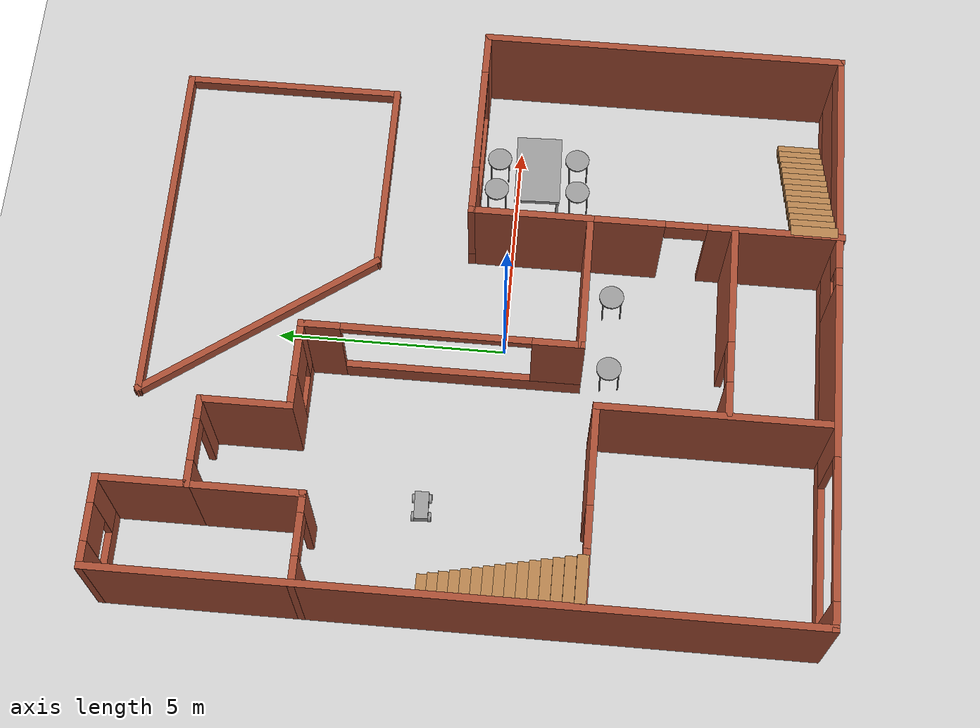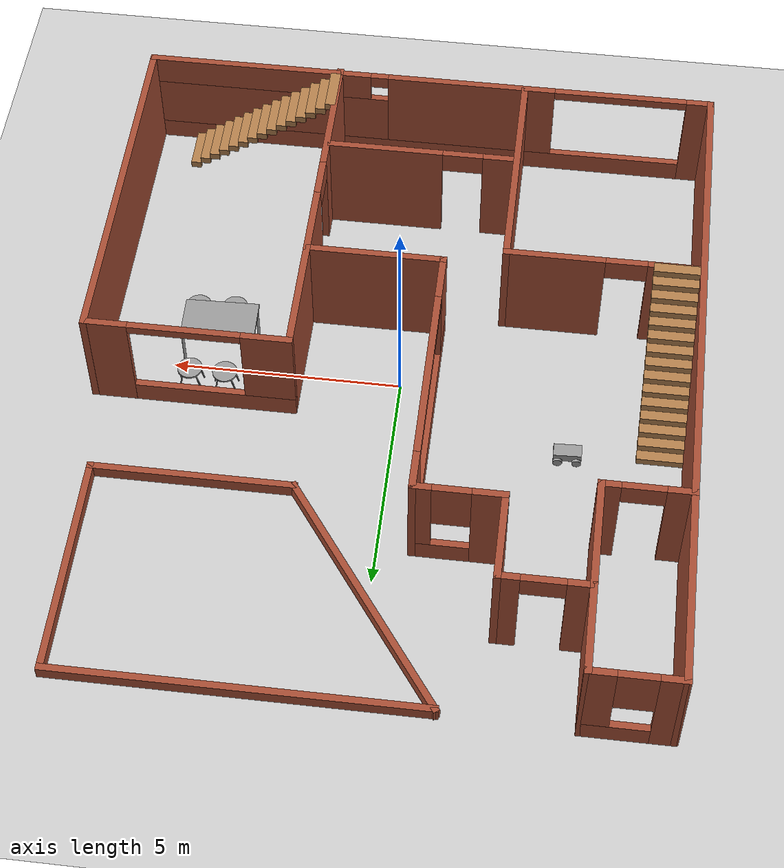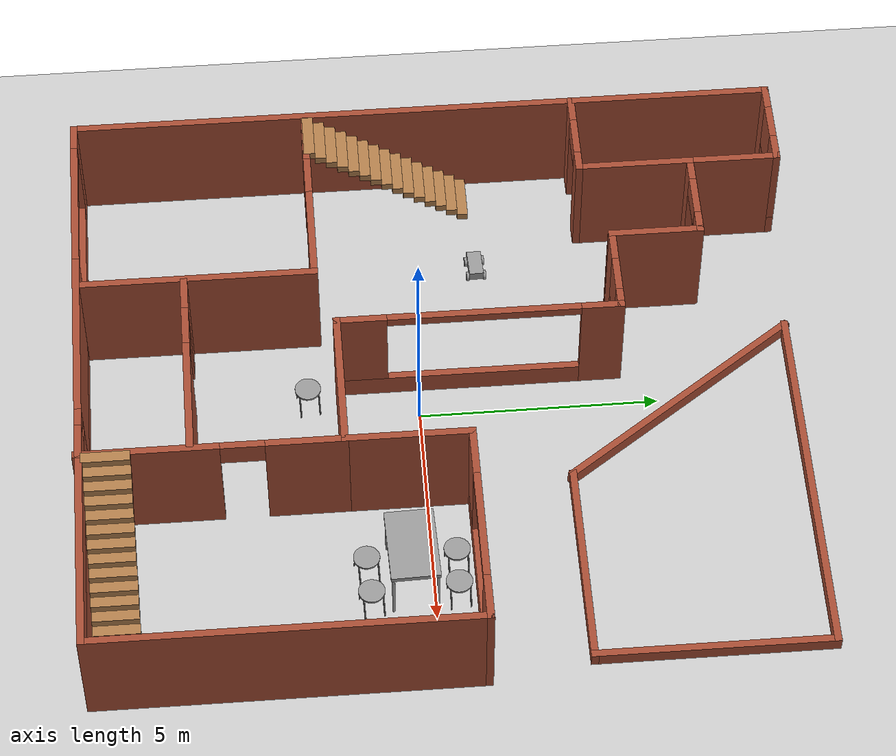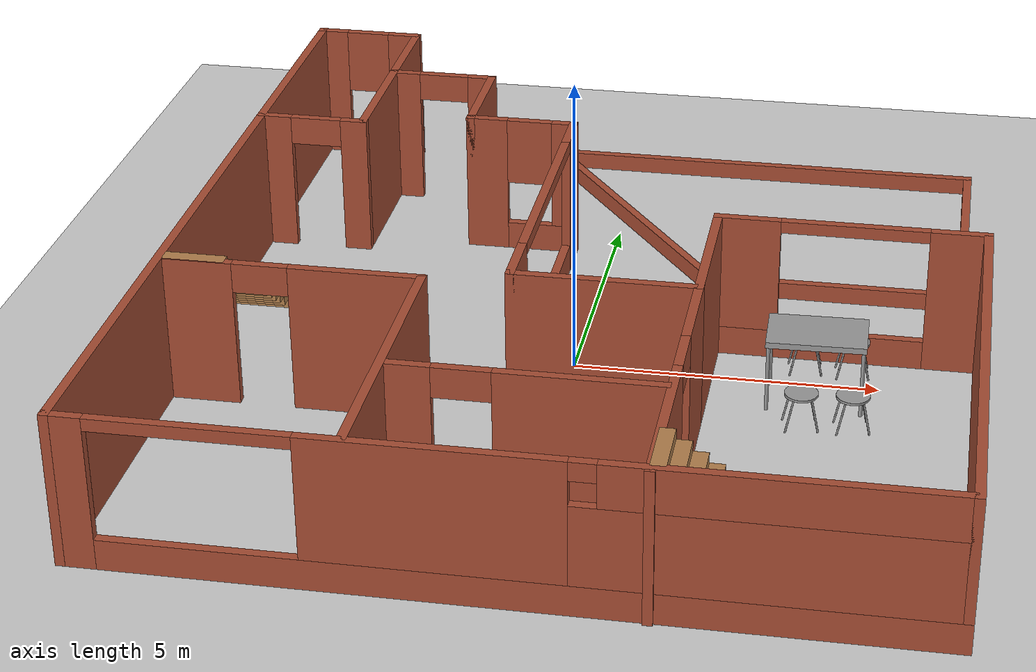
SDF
<sdf version="1.6">
 <world name="default">
  <plugin name="welcome" filename="libwelcome.so"/>
  <light name="sun" type="directional">
   <pose>0 0 10 0 -0 0</pose>
   <diffuse>0.8 0.8 0.8 1</diffuse>
   <specular>0.2 0.2 0.2 1</specular>
   <attenuation>
    <range>1000</range>
    <constant>0.9</constant>
    <linear>0.01</linear>
    <quadratic>0.001</quadratic>
   </attenuation>
   <direction>-0.5 0.1 -0.9</direction>
  </light>
  <model name="ground_plane">
   <static>1</static>
   <link name="link">
    <collision name="collision">
     <geometry><plane><normal>0 0 1</normal><size>100 100</size></plane></geometry>
     <surface><friction><ode><mu>100</mu><mu2>50</mu2></ode></friction></surface>
    </collision>
    <visual name="visual">
     <cast_shadows>0</cast_shadows>
     <geometry><plane><normal>0 0 1</normal><size>100 100</size></plane></geometry>
     <material>
      <script><uri>file://media/materials/scripts/gazebo.material</uri><name>Gazebo/Grey</name></script>
     </material>
    </visual>
   </link>
  </model>
  <gravity>0 0 -9.8</gravity>
  <magnetic_field>6e-06 2.3e-05 -4.2e-05</magnetic_field>
  <atmosphere type="adiabatic"/>
  <physics name="default_physics" default="0" type="ode">
   <max_step_size>0.001</max_step_size>
   <real_time_factor>1</real_time_factor>
   <real_time_update_rate>1000</real_time_update_rate>
  </physics>
  <scene><ambient>0.4 0.4 0.4 1</ambient><background>0.7 0.7 0.7 1</background><shadows>1</shadows></scene>
  <spherical_coordinates>
   <surface_model>EARTH_WGS84</surface_model>
   <latitude_deg>0</latitude_deg>
   <longitude_deg>0</longitude_deg>
   <elevation>0</elevation>
   <heading_deg>0</heading_deg>
  </spherical_coordinates>
  <model name="housebuilding">
   <pose>0.142168 0.463862 0 0 -0 0</pose>
   <link name="Stairs_0">
    <visual name="Stairs_0_Visual_0">
     <pose>5.43244 -6.86535 0.083333 0 -0 -1.5708</pose>
     <geometry><box><size>1 0.233333 0.166667</size></box></geometry>
     <material>
      <script><uri>file://media/materials/scripts/gazebo.material</uri><name>Gazebo/Wood</name></script>
      <ambient>1 1 1 1</ambient>
     </material>
     <meta><layer>0</layer></meta>
    </visual>
    <collision name="Stairs_0_Collision_0">
     <geometry><box><size>1 0.233333 0.166667</size></box></geometry>
     <pose>5.43244 -6.86535 0.083333 0 -0 -1.5708</pose>
    </collision>
    <visual name="Stairs_0_Visual_1">
     <pose>5.1991 -6.86535 0.25 0 -0 -1.5708</pose>
     <geometry><box><size>1 0.233333 0.166667</size></box></geometry>
     <material>
      <script><uri>file://media/materials/scripts/gazebo.material</uri><name>Gazebo/Wood</name></script>
      <ambient>1 1 1 1</ambient>
     </material>
     <meta><layer>0</layer></meta>
    </visual>
    <collision name="Stairs_0_Collision_1">
     <geometry><box><size>1 0.233333 0.166667</size></box></geometry>
     <pose>5.1991 -6.86535 0.25 0 -0 -1.5708</pose>
    </collision>
    <visual name="Stairs_0_Visual_2">
     <pose>4.96577 -6.86535 0.416667 0 -0 -1.5708</pose>
     <geometry><box><size>1 0.233333 0.166667</size></box></geometry>
     <material>
      <script><uri>file://media/materials/scripts/gazebo.material</uri><name>Gazebo/Wood</name></script>
      <ambient>1 1 1 1</ambient>
     </material>
     <meta><layer>0</layer></meta>
    </visual>
    <collision name="Stairs_0_Collision_2">
     <geometry><box><size>1 0.233333 0.166667</size></box></geometry>
     <pose>4.96577 -6.86535 0.416667 0 -0 -1.5708</pose>
    </collision>
    <visual name="Stairs_0_Visual_3">
     <pose>4.73244 -6.86535 0.583333 0 -0 -1.5708</pose>
     <geometry><box><size>1 0.233333 0.166667</size></box></geometry>
     <material>
      <script><uri>file://media/materials/scripts/gazebo.material</uri><name>Gazebo/Wood</name></script>
      <ambient>1 1 1 1</ambient>
     </material>
     <meta><layer>0</layer></meta>
    </visual>
    <collision name="Stairs_0_Collision_3">
     <geometry><box><size>1 0.233333 0.166667</size></box></geometry>
     <pose>4.73244 -6.86535 0.583333 0 -0 -1.5708</pose>
    </collision>
    <visual name="Stairs_0_Visual_4">
     <pose>4.4991 -6.86535 0.75 0 -0 -1.5708</pose>
     <geometry><box><size>1 0.233333 0.166667</size></box></geometry>
     <material>
      <script><uri>file://media/materials/scripts/gazebo.material</uri><name>Gazebo/Wood</name></script>
      <ambient>1 1 1 1</ambient>
     </material>
     <meta><layer>0</layer></meta>
    </visual>
    <collision name="Stairs_0_Collision_4">
     <geometry><box><size>1 0.233333 0.166667</size></box></geometry>
     <pose>4.4991 -6.86535 0.75 0 -0 -1.5708</pose>
    </collision>
    <visual name="Stairs_0_Visual_5">
     <pose>4.26577 -6.86535 0.916667 0 -0 -1.5708</pose>
     <geometry><box><size>1 0.233333 0.166667</size></box></geometry>
     <material>
      <script><uri>file://media/materials/scripts/gazebo.material</uri><name>Gazebo/Wood</name></script>
      <ambient>1 1 1 1</ambient>
     </material>
     <meta><layer>0</layer></meta>
    </visual>
    <collision name="Stairs_0_Collision_5">
     <geometry><box><size>1 0.233333 0.166667</size></box></geometry>
     <pose>4.26577 -6.86535 0.916667 0 -0 -1.5708</pose>
    </collision>
    <visual name="Stairs_0_Visual_6">
     <pose>4.03244 -6.86535 1.08333 0 -0 -1.5708</pose>
     <geometry><box><size>1 0.233333 0.166667</size></box></geometry>
     <material>
      <script><uri>file://media/materials/scripts/gazebo.material</uri><name>Gazebo/Wood</name></script>
      <ambient>1 1 1 1</ambient>
     </material>
     <meta><layer>0</layer></meta>
    </visual>
    <collision name="Stairs_0_Collision_6">
     <geometry><box><size>1 0.233333 0.166667</size></box></geometry>
     <pose>4.03244 -6.86535 1.08333 0 -0 -1.5708</pose>
    </collision>
    <visual name="Stairs_0_Visual_7">
     <pose>3.7991 -6.86535 1.25 0 -0 -1.5708</pose>
     <geometry><box><size>1 0.233333 0.166667</size></box></geometry>
     <material>
      <script><uri>file://media/materials/scripts/gazebo.material</uri><name>Gazebo/Wood</name></script>
      <ambient>1 1 1 1</ambient>
     </material>
     <meta><layer>0</layer></meta>
    </visual>
    <collision name="Stairs_0_Collision_7">
     <geometry><box><size>1 0.233333 0.166667</size></box></geometry>
     <pose>3.7991 -6.86535 1.25 0 -0 -1.5708</pose>
    </collision>
    <visual name="Stairs_0_Visual_8">
     <pose>3.56577 -6.86535 1.41667 0 -0 -1.5708</pose>
     <geometry><box><size>1 0.233333 0.166667</size></box></geometry>
     <material>
      <script><uri>file://media/materials/scripts/gazebo.material</uri><name>Gazebo/Wood</name></script>
      <ambient>1 1 1 1</ambient>
     </material>
     <meta><layer>0</layer></meta>
    </visual>
    <collision name="Stairs_0_Collision_8">
     <geometry><box><size>1 0.233333 0.166667</size></box></geometry>
     <pose>3.56577 -6.86535 1.41667 0 -0 -1.5708</pose>
    </collision>
    <visual name="Stairs_0_Visual_9">
     <pose>3.33244 -6.86535 1.58333 0 -0 -1.5708</pose>
     <geometry><box><size>1 0.233333 0.166667</size></box></geometry>
     <material>
      <script><uri>file://media/materials/scripts/gazebo.material</uri><name>Gazebo/Wood</name></script>
      <ambient>1 1 1 1</ambient>
     </material>
     <meta><layer>0</layer></meta>
    </visual>
    <collision name="Stairs_0_Collision_9">
     <geometry><box><size>1 0.233333 0.166667</size></box></geometry>
     <pose>3.33244 -6.86535 1.58333 0 -0 -1.5708</pose>
    </collision>
    <visual name="Stairs_0_Visual_10">
     <pose>3.0991 -6.86535 1.75 0 -0 -1.5708</pose>
     <geometry><box><size>1 0.233333 0.166667</size></box></geometry>
     <material>
      <script><uri>file://media/materials/scripts/gazebo.material</uri><name>Gazebo/Wood</name></script>
      <ambient>1 1 1 1</ambient>
     </material>
     <meta><layer>0</layer></meta>
    </visual>
    <collision name="Stairs_0_Collision_10">
     <geometry><box><size>1 0.233333 0.166667</size></box></geometry>
     <pose>3.0991 -6.86535 1.75 0 -0 -1.5708</pose>
    </collision>
    <visual name="Stairs_0_Visual_11">
     <pose>2.86577 -6.86535 1.91667 0 -0 -1.5708</pose>
     <geometry><box><size>1 0.233333 0.166667</size></box></geometry>
     <material>
      <script><uri>file://media/materials/scripts/gazebo.material</uri><name>Gazebo/Wood</name></script>
      <ambient>1 1 1 1</ambient>
     </material>
     <meta><layer>0</layer></meta>
    </visual>
    <collision name="Stairs_0_Collision_11">
     <geometry><box><size>1 0.233333 0.166667</size></box></geometry>
     <pose>2.86577 -6.86535 1.91667 0 -0 -1.5708</pose>
    </collision>
    <visual name="Stairs_0_Visual_12">
     <pose>2.63244 -6.86535 2.08333 0 -0 -1.5708</pose>
     <geometry><box><size>1 0.233333 0.166667</size></box></geometry>
     <material>
      <script><uri>file://media/materials/scripts/gazebo.material</uri><name>Gazebo/Wood</name></script>
      <ambient>1 1 1 1</ambient>
     </material>
     <meta><layer>0</layer></meta>
    </visual>
    <collision name="Stairs_0_Collision_12">
     <geometry><box><size>1 0.233333 0.166667</size></box></geometry>
     <pose>2.63244 -6.86535 2.08333 0 -0 -1.5708</pose>
    </collision>
    <visual name="Stairs_0_Visual_13">
     <pose>2.3991 -6.86535 2.25 0 -0 -1.5708</pose>
     <geometry><box><size>1 0.233333 0.166667</size></box></geometry>
     <material>
      <script><uri>file://media/materials/scripts/gazebo.material</uri><name>Gazebo/Wood</name></script>
      <ambient>1 1 1 1</ambient>
     </material>
     <meta><layer>0</layer></meta>
    </visual>
    <collision name="Stairs_0_Collision_13">
     <geometry><box><size>1 0.233333 0.166667</size></box></geometry>
     <pose>2.3991 -6.86535 2.25 0 -0 -1.5708</pose>
    </collision>
    <visual name="Stairs_0_Visual_14">
     <pose>2.16577 -6.86535 2.41667 0 -0 -1.5708</pose>
     <geometry><box><size>1 0.233333 0.166667</size></box></geometry>
     <material>
      <script><uri>file://media/materials/scripts/gazebo.material</uri><name>Gazebo/Wood</name></script>
      <ambient>1 1 1 1</ambient>
     </material>
     <meta><layer>0</layer></meta>
    </visual>
    <collision name="Stairs_0_Collision_14">
     <geometry><box><size>1 0.233333 0.166667</size></box></geometry>
     <pose>2.16577 -6.86535 2.41667 0 -0 -1.5708</pose>
    </collision>
   </link>
   <link name="Stairs_1">
    <visual name="Stairs_1_Visual_0">
     <pose>-5.85852 0.84566 0.083333 0 -0 0</pose>
     <geometry><box><size>1 0.233333 0.166667</size></box></geometry>
     <material>
      <script><uri>file://media/materials/scripts/gazebo.material</uri><name>Gazebo/Wood</name></script>
      <ambient>1 1 1 1</ambient>
     </material>
     <meta><layer>0</layer></meta>
    </visual>
    <collision name="Stairs_1_Collision_0">
     <geometry><box><size>1 0.233333 0.166667</size></box></geometry>
     <pose>-5.85852 0.84566 0.083333 0 -0 0</pose>
    </collision>
    <visual name="Stairs_1_Visual_1">
     <pose>-5.85852 0.612327 0.25 0 -0 0</pose>
     <geometry><box><size>1 0.233333 0.166667</size></box></geometry>
     <material>
      <script><uri>file://media/materials/scripts/gazebo.material</uri><name>Gazebo/Wood</name></script>
      <ambient>1 1 1 1</ambient>
     </material>
     <meta><layer>0</layer></meta>
    </visual>
    <collision name="Stairs_1_Collision_1">
     <geometry><box><size>1 0.233333 0.166667</size></box></geometry>
     <pose>-5.85852 0.612327 0.25 0 -0 0</pose>
    </collision>
    <visual name="Stairs_1_Visual_2">
     <pose>-5.85852 0.378993 0.416667 0 -0 0</pose>
     <geometry><box><size>1 0.233333 0.166667</size></box></geometry>
     <material>
      <script><uri>file://media/materials/scripts/gazebo.material</uri><name>Gazebo/Wood</name></script>
      <ambient>1 1 1 1</ambient>
     </material>
     <meta><layer>0</layer></meta>
    </visual>
    <collision name="Stairs_1_Collision_2">
     <geometry><box><size>1 0.233333 0.166667</size></box></geometry>
     <pose>-5.85852 0.378993 0.416667 0 -0 0</pose>
    </collision>
    <visual name="Stairs_1_Visual_3">
     <pose>-5.85852 0.14566 0.583333 0 -0 0</pose>
     <geometry><box><size>1 0.233333 0.166667</size></box></geometry>
     <material>
      <script><uri>file://media/materials/scripts/gazebo.material</uri><name>Gazebo/Wood</name></script>
      <ambient>1 1 1 1</ambient>
     </material>
     <meta><layer>0</layer></meta>
    </visual>
    <collision name="Stairs_1_Collision_3">
     <geometry><box><size>1 0.233333 0.166667</size></box></geometry>
     <pose>-5.85852 0.14566 0.583333 0 -0 0</pose>
    </collision>
    <visual name="Stairs_1_Visual_4">
     <pose>-5.85852 -0.087673 0.75 0 -0 0</pose>
     <geometry><box><size>1 0.233333 0.166667</size></box></geometry>
     <material>
      <script><uri>file://media/materials/scripts/gazebo.material</uri><name>Gazebo/Wood</name></script>
      <ambient>1 1 1 1</ambient>
     </material>
     <meta><layer>0</layer></meta>
    </visual>
    <collision name="Stairs_1_Collision_4">
     <geometry><box><size>1 0.233333 0.166667</size></box></geometry>
     <pose>-5.85852 -0.087673 0.75 0 -0 0</pose>
    </collision>
    <visual name="Stairs_1_Visual_5">
     <pose>-5.85852 -0.321007 0.916667 0 -0 0</pose>
     <geometry><box><size>1 0.233333 0.166667</size></box></geometry>
     <material>
      <script><uri>file://media/materials/scripts/gazebo.material</uri><name>Gazebo/Wood</name></script>
      <ambient>1 1 1 1</ambient>
     </material>
     <meta><layer>0</layer></meta>
    </visual>
    <collision name="Stairs_1_Collision_5">
     <geometry><box><size>1 0.233333 0.166667</size></box></geometry>
     <pose>-5.85852 -0.321007 0.916667 0 -0 0</pose>
    </collision>
    <visual name="Stairs_1_Visual_6">
     <pose>-5.85852 -0.55434 1.08333 0 -0 0</pose>
     <geometry><box><size>1 0.233333 0.166667</size></box></geometry>
     <material>
      <script><uri>file://media/materials/scripts/gazebo.material</uri><name>Gazebo/Wood</name></script>
      <ambient>1 1 1 1</ambient>
     </material>
     <meta><layer>0</layer></meta>
    </visual>
    <collision name="Stairs_1_Collision_6">
     <geometry><box><size>1 0.233333 0.166667</size></box></geometry>
     <pose>-5.85852 -0.55434 1.08333 0 -0 0</pose>
    </collision>
    <visual name="Stairs_1_Visual_7">
     <pose>-5.85852 -0.787673 1.25 0 -0 0</pose>
     <geometry><box><size>1 0.233333 0.166667</size></box></geometry>
     <material>
      <script><uri>file://media/materials/scripts/gazebo.material</uri><name>Gazebo/Wood</name></script>
      <ambient>1 1 1 1</ambient>
     </material>
     <meta><layer>0</layer></meta>
    </visual>
    <collision name="Stairs_1_Collision_7">
     <geometry><box><size>1 0.233333 0.166667</size></box></geometry>
     <pose>-5.85852 -0.787673 1.25 0 -0 0</pose>
    </collision>
    <visual name="Stairs_1_Visual_8">
     <pose>-5.85852 -1.02101 1.41667 0 -0 0</pose>
     <geometry><box><size>1 0.233333 0.166667</size></box></geometry>
     <material>
      <script><uri>file://media/materials/scripts/gazebo.material</uri><name>Gazebo/Wood</name></script>
      <ambient>1 1 1 1</ambient>
     </material>
     <meta><layer>0</layer></meta>
    </visual>
    <collision name="Stairs_1_Collision_8">
     <geometry><box><size>1 0.233333 0.166667</size></box></geometry>
     <pose>-5.85852 -1.02101 1.41667 0 -0 0</pose>
    </collision>
    <visual name="Stairs_1_Visual_9">
     <pose>-5.85852 -1.25434 1.58333 0 -0 0</pose>
     <geometry><box><size>1 0.233333 0.166667</size></box></geometry>
     <material>
      <script><uri>file://media/materials/scripts/gazebo.material</uri><name>Gazebo/Wood</name></script>
      <ambient>1 1 1 1</ambient>
     </material>
     <meta><layer>0</layer></meta>
    </visual>
    <collision name="Stairs_1_Collision_9">
     <geometry><box><size>1 0.233333 0.166667</size></box></geometry>
     <pose>-5.85852 -1.25434 1.58333 0 -0 0</pose>
    </collision>
    <visual name="Stairs_1_Visual_10">
     <pose>-5.85852 -1.48767 1.75 0 -0 0</pose>
     <geometry><box><size>1 0.233333 0.166667</size></box></geometry>
     <material>
      <script><uri>file://media/materials/scripts/gazebo.material</uri><name>Gazebo/Wood</name></script>
      <ambient>1 1 1 1</ambient>
     </material>
     <meta><layer>0</layer></meta>
    </visual>
    <collision name="Stairs_1_Collision_10">
     <geometry><box><size>1 0.233333 0.166667</size></box></geometry>
     <pose>-5.85852 -1.48767 1.75 0 -0 0</pose>
    </collision>
    <visual name="Stairs_1_Visual_11">
     <pose>-5.85852 -1.72101 1.91667 0 -0 0</pose>
     <geometry><box><size>1 0.233333 0.166667</size></box></geometry>
     <material>
      <script><uri>file://media/materials/scripts/gazebo.material</uri><name>Gazebo/Wood</name></script>
      <ambient>1 1 1 1</ambient>
     </material>
     <meta><layer>0</layer></meta>
    </visual>
    <collision name="Stairs_1_Collision_11">
     <geometry><box><size>1 0.233333 0.166667</size></box></geometry>
     <pose>-5.85852 -1.72101 1.91667 0 -0 0</pose>
    </collision>
    <visual name="Stairs_1_Visual_12">
     <pose>-5.85852 -1.95434 2.08333 0 -0 0</pose>
     <geometry><box><size>1 0.233333 0.166667</size></box></geometry>
     <material>
      <script><uri>file://media/materials/scripts/gazebo.material</uri><name>Gazebo/Wood</name></script>
      <ambient>1 1 1 1</ambient>
     </material>
     <meta><layer>0</layer></meta>
    </visual>
    <collision name="Stairs_1_Collision_12">
     <geometry><box><size>1 0.233333 0.166667</size></box></geometry>
     <pose>-5.85852 -1.95434 2.08333 0 -0 0</pose>
    </collision>
    <visual name="Stairs_1_Visual_13">
     <pose>-5.85852 -2.18767 2.25 0 -0 0</pose>
     <geometry><box><size>1 0.233333 0.166667</size></box></geometry>
     <material>
      <script><uri>file://media/materials/scripts/gazebo.material</uri><name>Gazebo/Wood</name></script>
      <ambient>1 1 1 1</ambient>
     </material>
     <meta><layer>0</layer></meta>
    </visual>
    <collision name="Stairs_1_Collision_13">
     <geometry><box><size>1 0.233333 0.166667</size></box></geometry>
     <pose>-5.85852 -2.18767 2.25 0 -0 0</pose>
    </collision>
    <visual name="Stairs_1_Visual_14">
     <pose>-5.85852 -2.42101 2.41667 0 -0 0</pose>
     <geometry><box><size>1 0.233333 0.166667</size></box></geometry>
     <material>
      <script><uri>file://media/materials/scripts/gazebo.material</uri><name>Gazebo/Wood</name></script>
      <ambient>1 1 1 1</ambient>
     </material>
     <meta><layer>0</layer></meta>
    </visual>
    <collision name="Stairs_1_Collision_14">
     <geometry><box><size>1 0.233333 0.166667</size></box></geometry>
     <pose>-5.85852 -2.42101 2.41667 0 -0 0</pose>
    </collision>
   </link>
   <link name="Wall_1">
    <collision name="Wall_1_Collision">
     <geometry><box><size>15 0.15 2.5</size></box></geometry>
     <pose>0 0 1.25 0 -0 0</pose>
    </collision>
    <visual name="Wall_1_Visual">
     <pose>0 0 1.25 0 -0 0</pose>
     <geometry><box><size>15 0.15 2.5</size></box></geometry>
     <material>
      <script><uri>file://media/materials/scripts/gazebo.material</uri><name>Gazebo/Bricks</name></script>
      <ambient>1 1 1 1</ambient>
     </material>
     <meta><layer>0</layer></meta>
    </visual>
    <pose>-6.42477 0.024996 0 0 0 -1.5708</pose>
   </link>
   <link name="Wall_11">
    <pose>-1.80023 3.74977 0 0 -0 0</pose>
    <visual name="Wall_11_Visual_0">
     <pose>-0.629965 0 1.25 0 -0 0</pose>
     <geometry><box><size>0.74007 0.15 2.5</size></box></geometry>
     <material>
      <script><uri>file://media/materials/scripts/gazebo.material</uri><name>Gazebo/Bricks</name></script>
      <ambient>1 1 1 1</ambient>
     </material>
     <meta><layer>0</layer></meta>
    </visual>
    <collision name="Wall_11_Collision_0">
     <geometry><box><size>0.74007 0.15 2.5</size></box></geometry>
     <pose>-0.629965 0 1.25 0 -0 0</pose>
    </collision>
    <visual name="Wall_11_Visual_1">
     <pose>0.370035 0 0.25 0 -0 0</pose>
     <geometry><box><size>1.25993 0.15 0.5</size></box></geometry>
     <material>
      <script><uri>file://media/materials/scripts/gazebo.material</uri><name>Gazebo/Bricks</name></script>
      <ambient>1 1 1 1</ambient>
     </material>
     <meta><layer>0</layer></meta>
    </visual>
    <collision name="Wall_11_Collision_1">
     <geometry><box><size>1.25993 0.15 0.5</size></box></geometry>
     <pose>0.370035 0 0.25 0 -0 0</pose>
    </collision>
    <visual name="Wall_11_Visual_2">
     <pose>0.770035 0 1.5 0 -0 0</pose>
     <geometry><box><size>0.45993 0.15 2</size></box></geometry>
     <material>
      <script><uri>file://media/materials/scripts/gazebo.material</uri><name>Gazebo/Bricks</name></script>
      <ambient>1 1 1 1</ambient>
     </material>
     <meta><layer>0</layer></meta>
    </visual>
    <collision name="Wall_11_Collision_2">
     <geometry><box><size>0.45993 0.15 2</size></box></geometry>
     <pose>0.770035 0 1.5 0 -0 0</pose>
    </collision>
    <visual name="Wall_11_Visual_3">
     <pose>0.14007 0 1.9 0 -0 0</pose>
     <geometry><box><size>0.8 0.15 1.2</size></box></geometry>
     <material>
      <script><uri>file://media/materials/scripts/gazebo.material</uri><name>Gazebo/Bricks</name></script>
      <ambient>1 1 1 1</ambient>
     </material>
     <meta><layer>0</layer></meta>
    </visual>
    <collision name="Wall_11_Collision_3">
     <geometry><box><size>0.8 0.15 1.2</size></box></geometry>
     <pose>0.14007 0 1.9 0 -0 0</pose>
    </collision>
   </link>
   <link name="Wall_13">
    <pose>-0.875232 0.824773 0 0 0 -1.5708</pose>
    <visual name="Wall_13_Visual_0">
     <pose>-2.55253 0 1.25 0 -0 0</pose>
     <geometry><box><size>0.894936 0.15 2.5</size></box></geometry>
     <material>
      <script><uri>file://media/materials/scripts/gazebo.material</uri><name>Gazebo/Bricks</name></script>
      <ambient>1 1 1 1</ambient>
     </material>
     <meta><layer>0</layer></meta>
    </visual>
    <collision name="Wall_13_Collision_0">
     <geometry><box><size>0.894936 0.15 2.5</size></box></geometry>
     <pose>-2.55253 0 1.25 0 -0 0</pose>
    </collision>
    <visual name="Wall_13_Visual_1">
     <pose>0.447468 0 0.25 0 -0 0</pose>
     <geometry><box><size>5.10506 0.15 0.5</size></box></geometry>
     <material>
      <script><uri>file://media/materials/scripts/gazebo.material</uri><name>Gazebo/Bricks</name></script>
      <ambient>1 1 1 1</ambient>
     </material>
     <meta><layer>0</layer></meta>
    </visual>
    <collision name="Wall_13_Collision_1">
     <geometry><box><size>5.10506 0.15 0.5</size></box></geometry>
     <pose>0.447468 0 0.25 0 -0 0</pose>
    </collision>
    <visual name="Wall_13_Visual_2">
     <pose>2.44747 0 1.5 0 -0 0</pose>
     <geometry><box><size>1.10506 0.15 2</size></box></geometry>
     <material>
      <script><uri>file://media/materials/scripts/gazebo.material</uri><name>Gazebo/Bricks</name></script>
      <ambient>1 1 1 1</ambient>
     </material>
     <meta><layer>0</layer></meta>
    </visual>
    <collision name="Wall_13_Collision_2">
     <geometry><box><size>1.10506 0.15 2</size></box></geometry>
     <pose>2.44747 0 1.5 0 -0 0</pose>
    </collision>
    <visual name="Wall_13_Visual_3">
     <pose>-0.105064 0 2.4 0 -0 0</pose>
     <geometry><box><size>4 0.15 0.2</size></box></geometry>
     <material>
      <script><uri>file://media/materials/scripts/gazebo.material</uri><name>Gazebo/Bricks</name></script>
      <ambient>1 1 1 1</ambient>
     </material>
     <meta><layer>0</layer></meta>
    </visual>
    <collision name="Wall_13_Collision_3">
     <geometry><box><size>4 0.15 0.2</size></box></geometry>
     <pose>-0.105064 0 2.4 0 -0 0</pose>
    </collision>
   </link>
   <link name="Wall_15">
    <collision name="Wall_15_Collision">
     <geometry><box><size>3 0.15 2.5</size></box></geometry>
     <pose>0 0 1.25 0 -0 0</pose>
    </collision>
    <visual name="Wall_15_Visual">
     <pose>0 0 1.25 0 -0 0</pose>
     <geometry><box><size>3 0.15 2.5</size></box></geometry>
     <material>
      <script><uri>file://media/materials/scripts/gazebo.material</uri><name>Gazebo/Bricks</name></script>
      <ambient>1 1 1 1</ambient>
     </material>
     <meta><layer>0</layer></meta>
    </visual>
    <pose>0.549768 -2.10023 0 0 -0 0</pose>
   </link>
   <link name="Wall_17">
    <pose>0.000231 -7.4 0 0 -0 0</pose>
    <visual name="Wall_17_Visual_0">
     <pose>-6.18989 0 1.25 0 -0 0</pose>
     <geometry><box><size>0.620214 0.15 2.5</size></box></geometry>
     <material>
      <script><uri>file://media/materials/scripts/gazebo.material</uri><name>Gazebo/Bricks</name></script>
      <ambient>1 1 1 1</ambient>
     </material>
     <meta><layer>0</layer></meta>
    </visual>
    <collision name="Wall_17_Collision_0">
     <geometry><box><size>0.620214 0.15 2.5</size></box></geometry>
     <pose>-6.18989 0 1.25 0 -0 0</pose>
    </collision>
    <visual name="Wall_17_Visual_1">
     <pose>0.310107 0 0.25 0 -0 0</pose>
     <geometry><box><size>12.3798 0.15 0.5</size></box></geometry>
     <material>
      <script><uri>file://media/materials/scripts/gazebo.material</uri><name>Gazebo/Bricks</name></script>
      <ambient>1 1 1 1</ambient>
     </material>
     <meta><layer>0</layer></meta>
    </visual>
    <collision name="Wall_17_Collision_1">
     <geometry><box><size>12.3798 0.15 0.5</size></box></geometry>
     <pose>0.310107 0 0.25 0 -0 0</pose>
    </collision>
    <visual name="Wall_17_Visual_2">
     <pose>-0.962685 0 1.5 0 -0 0</pose>
     <geometry><box><size>3.8342 0.15 2</size></box></geometry>
     <material>
      <script><uri>file://media/materials/scripts/gazebo.material</uri><name>Gazebo/Bricks</name></script>
      <ambient>1 1 1 1</ambient>
     </material>
     <meta><layer>0</layer></meta>
    </visual>
    <collision name="Wall_17_Collision_2">
     <geometry><box><size>3.8342 0.15 2</size></box></geometry>
     <pose>-0.962685 0 1.5 0 -0 0</pose>
    </collision>
    <visual name="Wall_17_Visual_3">
     <pose>3.72721 0 1.15 0 -0 0</pose>
     <geometry><box><size>5.54558 0.15 1.3</size></box></geometry>
     <material>
      <script><uri>file://media/materials/scripts/gazebo.material</uri><name>Gazebo/Bricks</name></script>
      <ambient>1 1 1 1</ambient>
     </material>
     <meta><layer>0</layer></meta>
    </visual>
    <collision name="Wall_17_Collision_3">
     <geometry><box><size>5.54558 0.15 1.3</size></box></geometry>
     <pose>3.72721 0 1.15 0 -0 0</pose>
    </collision>
    <visual name="Wall_17_Visual_4">
     <pose>3.92721 0 2.15 0 -0 0</pose>
     <geometry><box><size>5.14558 0.15 0.7</size></box></geometry>
     <material>
      <script><uri>file://media/materials/scripts/gazebo.material</uri><name>Gazebo/Bricks</name></script>
      <ambient>1 1 1 1</ambient>
     </material>
     <meta><layer>0</layer></meta>
    </visual>
    <collision name="Wall_17_Collision_4">
     <geometry><box><size>5.14558 0.15 0.7</size></box></geometry>
     <pose>3.92721 0 2.15 0 -0 0</pose>
    </collision>
    <visual name="Wall_17_Visual_5">
     <pose>1.15442 0 2.35 0 -0 0</pose>
     <geometry><box><size>0.4 0.15 0.3</size></box></geometry>
     <material>
      <script><uri>file://media/materials/scripts/gazebo.material</uri><name>Gazebo/Bricks</name></script>
      <ambient>1 1 1 1</ambient>
     </material>
     <meta><layer>0</layer></meta>
    </visual>
    <collision name="Wall_17_Collision_5">
     <geometry><box><size>0.4 0.15 0.3</size></box></geometry>
     <pose>1.15442 0 2.35 0 -0 0</pose>
    </collision>
    <visual name="Wall_17_Visual_6">
     <pose>-4.37979 0 2.4 0 -0 0</pose>
     <geometry><box><size>3 0.15 0.2</size></box></geometry>
     <material>
      <script><uri>file://media/materials/scripts/gazebo.material</uri><name>Gazebo/Bricks</name></script>
      <ambient>1 1 1 1</ambient>
     </material>
     <meta><layer>0</layer></meta>
    </visual>
    <collision name="Wall_17_Collision_6">
     <geometry><box><size>3 0.15 0.2</size></box></geometry>
     <pose>-4.37979 0 2.4 0 -0 0</pose>
    </collision>
   </link>
   <link name="Wall_19">
    <collision name="Wall_19_Collision">
     <geometry><box><size>8 0.15 2.5</size></box></geometry>
     <pose>0 0 1.25 0 -0 0</pose>
    </collision>
    <visual name="Wall_19_Visual">
     <pose>0 0 1.25 0 -0 0</pose>
     <geometry><box><size>8 0.15 2.5</size></box></geometry>
     <material>
      <script><uri>file://media/materials/scripts/gazebo.material</uri><name>Gazebo/Bricks</name></script>
      <ambient>1 1 1 1</ambient>
     </material>
     <meta><layer>0</layer></meta>
    </visual>
    <pose>6.42523 -3.475 0 0 -0 1.5708</pose>
   </link>
   <link name="Wall_21">
    <pose>4.25023 0.449996 0 0 -0 3.14159</pose>
    <visual name="Wall_21_Visual_0">
     <pose>-1.75159 0 1.25 0 -0 0</pose>
     <geometry><box><size>0.996815 0.15 2.5</size></box></geometry>
     <material>
      <script><uri>file://media/materials/scripts/gazebo.material</uri><name>Gazebo/Bricks</name></script>
      <ambient>1 1 1 1</ambient>
     </material>
     <meta><layer>0</layer></meta>
    </visual>
    <collision name="Wall_21_Collision_0">
     <geometry><box><size>0.996815 0.15 2.5</size></box></geometry>
     <pose>-1.75159 0 1.25 0 -0 0</pose>
    </collision>
    <visual name="Wall_21_Visual_1">
     <pose>0.498407 0 0.25 0 -0 0</pose>
     <geometry><box><size>3.50319 0.15 0.5</size></box></geometry>
     <material>
      <script><uri>file://media/materials/scripts/gazebo.material</uri><name>Gazebo/Bricks</name></script>
      <ambient>1 1 1 1</ambient>
     </material>
     <meta><layer>0</layer></meta>
    </visual>
    <collision name="Wall_21_Collision_1">
     <geometry><box><size>3.50319 0.15 0.5</size></box></geometry>
     <pose>0.498407 0 0.25 0 -0 0</pose>
    </collision>
    <visual name="Wall_21_Visual_2">
     <pose>1.69841 0 1.5 0 -0 0</pose>
     <geometry><box><size>1.10319 0.15 2</size></box></geometry>
     <material>
      <script><uri>file://media/materials/scripts/gazebo.material</uri><name>Gazebo/Bricks</name></script>
      <ambient>1 1 1 1</ambient>
     </material>
     <meta><layer>0</layer></meta>
    </visual>
    <collision name="Wall_21_Collision_2">
     <geometry><box><size>1.10319 0.15 2</size></box></geometry>
     <pose>1.69841 0 1.5 0 -0 0</pose>
    </collision>
    <visual name="Wall_21_Visual_3">
     <pose>-0.053185 0 2.4 0 -0 0</pose>
     <geometry><box><size>2.4 0.15 0.2</size></box></geometry>
     <material>
      <script><uri>file://media/materials/scripts/gazebo.material</uri><name>Gazebo/Bricks</name></script>
      <ambient>1 1 1 1</ambient>
     </material>
     <meta><layer>0</layer></meta>
    </visual>
    <collision name="Wall_21_Collision_3">
     <geometry><box><size>2.4 0.15 0.2</size></box></geometry>
     <pose>-0.053185 0 2.4 0 -0 0</pose>
    </collision>
   </link>
   <link name="Wall_22">
    <collision name="Wall_22_Collision">
     <geometry><box><size>2.7 0.15 2.5</size></box></geometry>
     <pose>0 0 1.25 0 -0 0</pose>
    </collision>
    <visual name="Wall_22_Visual">
     <pose>0 0 1.25 0 -0 0</pose>
     <geometry><box><size>2.7 0.15 2.5</size></box></geometry>
     <material>
      <script><uri>file://media/materials/scripts/gazebo.material</uri><name>Gazebo/Bricks</name></script>
      <ambient>1 1 1 1</ambient>
     </material>
     <meta><layer>0</layer></meta>
    </visual>
    <pose>2.07523 -0.825004 0 0 0 -1.5708</pose>
   </link>
   <link name="Wall_28">
    <pose>-4.24345 -2.48646 0 0 -0 3.14159</pose>
    <visual name="Wall_28_Visual_0">
     <pose>-1.02115 0 1.25 0 -0 0</pose>
     <geometry><box><size>2.2077 0.15 2.5</size></box></geometry>
     <material>
      <script><uri>file://media/materials/scripts/gazebo.material</uri><name>Gazebo/Bricks</name></script>
      <ambient>1 1 1 1</ambient>
     </material>
     <meta><layer>0</layer></meta>
    </visual>
    <collision name="Wall_28_Collision_0">
     <geometry><box><size>2.2077 0.15 2.5</size></box></geometry>
     <pose>-1.02115 0 1.25 0 -0 0</pose>
    </collision>
    <visual name="Wall_28_Visual_1">
     <pose>1.55385 0 1.25 0 -0 0</pose>
     <geometry><box><size>1.1423 0.15 2.5</size></box></geometry>
     <material>
      <script><uri>file://media/materials/scripts/gazebo.material</uri><name>Gazebo/Bricks</name></script>
      <ambient>1 1 1 1</ambient>
     </material>
     <meta><layer>0</layer></meta>
    </visual>
    <collision name="Wall_28_Collision_1">
     <geometry><box><size>1.1423 0.15 2.5</size></box></geometry>
     <pose>1.55385 0 1.25 0 -0 0</pose>
    </collision>
    <visual name="Wall_28_Visual_2">
     <pose>0.532703 0 2.25 0 -0 0</pose>
     <geometry><box><size>0.9 0.15 0.5</size></box></geometry>
     <material>
      <script><uri>file://media/materials/scripts/gazebo.material</uri><name>Gazebo/Bricks</name></script>
      <ambient>1 1 1 1</ambient>
     </material>
     <meta><layer>0</layer></meta>
    </visual>
    <collision name="Wall_28_Collision_2">
     <geometry><box><size>0.9 0.15 0.5</size></box></geometry>
     <pose>0.532703 0 2.25 0 -0 0</pose>
    </collision>
   </link>
   <link name="Wall_3">
    <pose>-5.5 7.44988 0 0 0 -0.000121</pose>
    <visual name="Wall_3_Visual_0">
     <pose>-0.712281 0 1.25 0 -0 0</pose>
     <geometry><box><size>0.575437 0.15 2.5</size></box></geometry>
     <material>
      <script><uri>file://media/materials/scripts/gazebo.material</uri><name>Gazebo/Bricks</name></script>
      <ambient>1 1 1 1</ambient>
     </material>
     <meta><layer>0</layer></meta>
    </visual>
    <collision name="Wall_3_Collision_0">
     <geometry><box><size>0.575437 0.15 2.5</size></box></geometry>
     <pose>-0.712281 0 1.25 0 -0 0</pose>
    </collision>
    <visual name="Wall_3_Visual_1">
     <pose>0.287719 0 0.25 0 -0 0</pose>
     <geometry><box><size>1.42456 0.15 0.5</size></box></geometry>
     <material>
      <script><uri>file://media/materials/scripts/gazebo.material</uri><name>Gazebo/Bricks</name></script>
      <ambient>1 1 1 1</ambient>
     </material>
     <meta><layer>0</layer></meta>
    </visual>
    <collision name="Wall_3_Collision_1">
     <geometry><box><size>1.42456 0.15 0.5</size></box></geometry>
     <pose>0.287719 0 0.25 0 -0 0</pose>
    </collision>
    <visual name="Wall_3_Visual_2">
     <pose>0.687719 0 1.5 0 -0 0</pose>
     <geometry><box><size>0.624563 0.15 2</size></box></geometry>
     <material>
      <script><uri>file://media/materials/scripts/gazebo.material</uri><name>Gazebo/Bricks</name></script>
      <ambient>1 1 1 1</ambient>
     </material>
     <meta><layer>0</layer></meta>
    </visual>
    <collision name="Wall_3_Collision_2">
     <geometry><box><size>0.624563 0.15 2</size></box></geometry>
     <pose>0.687719 0 1.5 0 -0 0</pose>
    </collision>
    <visual name="Wall_3_Visual_3">
     <pose>-0.024563 0 1.9 0 -0 0</pose>
     <geometry><box><size>0.8 0.15 1.2</size></box></geometry>
     <material>
      <script><uri>file://media/materials/scripts/gazebo.material</uri><name>Gazebo/Bricks</name></script>
      <ambient>1 1 1 1</ambient>
     </material>
     <meta><layer>0</layer></meta>
    </visual>
    <collision name="Wall_3_Collision_3">
     <geometry><box><size>0.8 0.15 1.2</size></box></geometry>
     <pose>-0.024563 0 1.9 0 -0 0</pose>
    </collision>
   </link>
   <link name="Wall_30">
    <collision name="Wall_30_Collision">
     <geometry><box><size>5 0.15 2.5</size></box></geometry>
     <pose>0 0 1.25 0 -0 0</pose>
    </collision>
    <visual name="Wall_30_Visual">
     <pose>0 0 1.25 0 -0 0</pose>
     <geometry><box><size>5 0.15 2.5</size></box></geometry>
     <material>
      <script><uri>file://media/materials/scripts/gazebo.material</uri><name>Gazebo/Bricks</name></script>
      <ambient>1 1 1 1</ambient>
     </material>
     <meta><layer>0</layer></meta>
    </visual>
    <pose>-2.19345 -4.91146 0 0 0 -1.5708</pose>
   </link>
   <link name="Wall_34">
    <pose>-0.071706 -5.18421 0 0 -0 0</pose>
    <visual name="Wall_34_Visual_0">
     <pose>-1.74498 0 1.25 0 -0 0</pose>
     <geometry><box><size>0.760033 0.15 2.5</size></box></geometry>
     <material>
      <script><uri>file://media/materials/scripts/gazebo.material</uri><name>Gazebo/Bricks</name></script>
      <ambient>1 1 1 1</ambient>
     </material>
     <meta><layer>0</layer></meta>
    </visual>
    <collision name="Wall_34_Collision_0">
     <geometry><box><size>0.760033 0.15 2.5</size></box></geometry>
     <pose>-1.74498 0 1.25 0 -0 0</pose>
    </collision>
    <visual name="Wall_34_Visual_1">
     <pose>0.830017 0 1.25 0 -0 0</pose>
     <geometry><box><size>2.58997 0.15 2.5</size></box></geometry>
     <material>
      <script><uri>file://media/materials/scripts/gazebo.material</uri><name>Gazebo/Bricks</name></script>
      <ambient>1 1 1 1</ambient>
     </material>
     <meta><layer>0</layer></meta>
    </visual>
    <collision name="Wall_34_Collision_1">
     <geometry><box><size>2.58997 0.15 2.5</size></box></geometry>
     <pose>0.830017 0 1.25 0 -0 0</pose>
    </collision>
    <visual name="Wall_34_Visual_2">
     <pose>-0.914967 0 2.25 0 -0 0</pose>
     <geometry><box><size>0.9 0.15 0.5</size></box></geometry>
     <material>
      <script><uri>file://media/materials/scripts/gazebo.material</uri><name>Gazebo/Bricks</name></script>
      <ambient>1 1 1 1</ambient>
     </material>
     <meta><layer>0</layer></meta>
    </visual>
    <collision name="Wall_34_Collision_2">
     <geometry><box><size>0.9 0.15 0.5</size></box></geometry>
     <pose>-0.914967 0 2.25 0 -0 0</pose>
    </collision>
   </link>
   <link name="Wall_43">
    <pose>2.07523 -4.775 0 0 0 -1.5708</pose>
    <visual name="Wall_43_Visual_0">
     <pose>-1.91553 0 1.25 0 -0 0</pose>
     <geometry><box><size>1.66894 0.15 2.5</size></box></geometry>
     <material>
      <script><uri>file://media/materials/scripts/gazebo.material</uri><name>Gazebo/Bricks</name></script>
      <ambient>1 1 1 1</ambient>
     </material>
     <meta><layer>0</layer></meta>
    </visual>
    <collision name="Wall_43_Collision_0">
     <geometry><box><size>1.66894 0.15 2.5</size></box></geometry>
     <pose>-1.91553 0 1.25 0 -0 0</pose>
    </collision>
    <visual name="Wall_43_Visual_1">
     <pose>1.28447 0 1.25 0 -0 0</pose>
     <geometry><box><size>2.93106 0.15 2.5</size></box></geometry>
     <material>
      <script><uri>file://media/materials/scripts/gazebo.material</uri><name>Gazebo/Bricks</name></script>
      <ambient>1 1 1 1</ambient>
     </material>
     <meta><layer>0</layer></meta>
    </visual>
    <collision name="Wall_43_Collision_1">
     <geometry><box><size>2.93106 0.15 2.5</size></box></geometry>
     <pose>1.28447 0 1.25 0 -0 0</pose>
    </collision>
    <visual name="Wall_43_Visual_2">
     <pose>-0.631055 0 2.25 0 -0 0</pose>
     <geometry><box><size>0.9 0.15 0.5</size></box></geometry>
     <material>
      <script><uri>file://media/materials/scripts/gazebo.material</uri><name>Gazebo/Bricks</name></script>
      <ambient>1 1 1 1</ambient>
     </material>
     <meta><layer>0</layer></meta>
    </visual>
    <collision name="Wall_43_Collision_2">
     <geometry><box><size>0.9 0.15 0.5</size></box></geometry>
     <pose>-0.631055 0 2.25 0 -0 0</pose>
    </collision>
   </link>
   <link name="Wall_45">
    <collision name="Wall_45_Collision">
     <geometry><box><size>2.5 0.15 2.5</size></box></geometry>
     <pose>0 0 1.25 0 -0 0</pose>
    </collision>
    <visual name="Wall_45_Visual">
     <pose>0 0 1.25 0 -0 0</pose>
     <geometry><box><size>2.5 0.15 2.5</size></box></geometry>
     <material>
      <script><uri>file://media/materials/scripts/gazebo.material</uri><name>Gazebo/Bricks</name></script>
      <ambient>1 1 1 1</ambient>
     </material>
     <meta><layer>0</layer></meta>
    </visual>
    <pose>-4.57523 4.42477 0 0 0 -1.5708</pose>
   </link>
   <link name="Wall_47">
    <pose>-5.50023 3.24977 0 0 -0 3.14159</pose>
    <visual name="Wall_47_Visual_0">
     <pose>-0.762292 0 1.25 0 -0 0</pose>
     <geometry><box><size>0.475417 0.15 2.5</size></box></geometry>
     <material>
      <script><uri>file://media/materials/scripts/gazebo.material</uri><name>Gazebo/Bricks</name></script>
      <ambient>1 1 1 1</ambient>
     </material>
     <meta><layer>0</layer></meta>
    </visual>
    <collision name="Wall_47_Collision_0">
     <geometry><box><size>0.475417 0.15 2.5</size></box></geometry>
     <pose>-0.762292 0 1.25 0 -0 0</pose>
    </collision>
    <visual name="Wall_47_Visual_1">
     <pose>0.687708 0 1.25 0 -0 0</pose>
     <geometry><box><size>0.624583 0.15 2.5</size></box></geometry>
     <material>
      <script><uri>file://media/materials/scripts/gazebo.material</uri><name>Gazebo/Bricks</name></script>
      <ambient>1 1 1 1</ambient>
     </material>
     <meta><layer>0</layer></meta>
    </visual>
    <collision name="Wall_47_Collision_1">
     <geometry><box><size>0.624583 0.15 2.5</size></box></geometry>
     <pose>0.687708 0 1.25 0 -0 0</pose>
    </collision>
    <visual name="Wall_47_Visual_2">
     <pose>-0.074583 0 2.25 0 -0 0</pose>
     <geometry><box><size>0.9 0.15 0.5</size></box></geometry>
     <material>
      <script><uri>file://media/materials/scripts/gazebo.material</uri><name>Gazebo/Bricks</name></script>
      <ambient>1 1 1 1</ambient>
     </material>
     <meta><layer>0</layer></meta>
    </visual>
    <collision name="Wall_47_Collision_2">
     <geometry><box><size>0.9 0.15 0.5</size></box></geometry>
     <pose>-0.074583 0 2.25 0 -0 0</pose>
    </collision>
   </link>
   <link name="Wall_49">
    <collision name="Wall_49_Collision">
     <geometry><box><size>8 0.15 0.3</size></box></geometry>
     <pose>0 0 0.15 0 -0 0</pose>
    </collision>
    <visual name="Wall_49_Visual">
     <pose>0 0 0.15 0 -0 0</pose>
     <geometry><box><size>8 0.15 0.3</size></box></geometry>
     <material>
      <script><uri>file://media/materials/scripts/gazebo.material</uri><name>Gazebo/Bricks</name></script>
      <ambient>1 1 1 1</ambient>
     </material>
     <meta><layer>0</layer></meta>
    </visual>
    <pose>2.16977 7.41777 0 0 -0 0</pose>
   </link>
   <link name="Wall_5">
    <collision name="Wall_5_Collision">
     <geometry><box><size>2 0.15 2.5</size></box></geometry>
     <pose>0 0 1.25 0 -0 0</pose>
    </collision>
    <visual name="Wall_5_Visual">
     <pose>0 0 1.25 0 -0 0</pose>
     <geometry><box><size>2 0.15 2.5</size></box></geometry>
     <material>
      <script><uri>file://media/materials/scripts/gazebo.material</uri><name>Gazebo/Bricks</name></script>
      <ambient>1 1 1 1</ambient>
     </material>
     <meta><layer>0</layer></meta>
    </visual>
    <pose>-4.57523 6.52477 0 0 0 -1.5708</pose>
   </link>
   <link name="Wall_51">
    <collision name="Wall_51_Collision">
     <geometry><box><size>5 0.15 0.3</size></box></geometry>
     <pose>0 0 0.15 0 -0 0</pose>
    </collision>
    <visual name="Wall_51_Visual">
     <pose>0 0 0.15 0 -0 0</pose>
     <geometry><box><size>5 0.15 0.3</size></box></geometry>
     <material>
      <script><uri>file://media/materials/scripts/gazebo.material</uri><name>Gazebo/Bricks</name></script>
      <ambient>1 1 1 1</ambient>
     </material>
     <meta><layer>0</layer></meta>
    </visual>
    <pose>6.09477 4.99277 0 0 0 -1.5708</pose>
   </link>
   <link name="Wall_52">
    <collision name="Wall_52_Collision">
     <geometry><box><size>4.5 0.15 0.3</size></box></geometry>
     <pose>0 0 0.15 0 -0 0</pose>
    </collision>
    <visual name="Wall_52_Visual">
     <pose>0 0 0.15 0 -0 0</pose>
     <geometry><box><size>4.5 0.15 0.3</size></box></geometry>
     <material>
      <script><uri>file://media/materials/scripts/gazebo.material</uri><name>Gazebo/Bricks</name></script>
      <ambient>1 1 1 1</ambient>
     </material>
     <meta><layer>0</layer></meta>
    </visual>
    <pose>3.91977 2.56777 0 0 -0 3.14159</pose>
   </link>
   <link name="Wall_53">
    <collision name="Wall_53_Collision">
     <geometry><box><size>6.13101 0.15 0.3</size></box></geometry>
     <pose>0 0 0.15 0 -0 0</pose>
    </collision>
    <visual name="Wall_53_Visual">
     <pose>0 0 0.15 0 -0 0</pose>
     <geometry><box><size>6.13101 0.15 0.3</size></box></geometry>
     <material>
      <script><uri>file://media/materials/scripts/gazebo.material</uri><name>Gazebo/Bricks</name></script>
      <ambient>1 1 1 1</ambient>
     </material>
     <meta><layer>0</layer></meta>
    </visual>
    <pose>-0.005231 4.99277 0 0 -0 2.19591</pose>
   </link>
   <link name="Wall_7">
    <pose>-3.65023 5.59977 0 0 -0 0</pose>
    <visual name="Wall_7_Visual_0">
     <pose>-0.707992 0 1.25 0 -0 0</pose>
     <geometry><box><size>0.584016 0.15 2.5</size></box></geometry>
     <material>
      <script><uri>file://media/materials/scripts/gazebo.material</uri><name>Gazebo/Bricks</name></script>
      <ambient>1 1 1 1</ambient>
     </material>
     <meta><layer>0</layer></meta>
    </visual>
    <collision name="Wall_7_Collision_0">
     <geometry><box><size>0.584016 0.15 2.5</size></box></geometry>
     <pose>-0.707992 0 1.25 0 -0 0</pose>
    </collision>
    <visual name="Wall_7_Visual_1">
     <pose>0.742008 0 1.25 0 -0 0</pose>
     <geometry><box><size>0.515984 0.15 2.5</size></box></geometry>
     <material>
      <script><uri>file://media/materials/scripts/gazebo.material</uri><name>Gazebo/Bricks</name></script>
      <ambient>1 1 1 1</ambient>
     </material>
     <meta><layer>0</layer></meta>
    </visual>
    <collision name="Wall_7_Collision_1">
     <geometry><box><size>0.515984 0.15 2.5</size></box></geometry>
     <pose>0.742008 0 1.25 0 -0 0</pose>
    </collision>
    <visual name="Wall_7_Visual_2">
     <pose>0.034016 0 2.25 0 -0 0</pose>
     <geometry><box><size>0.9 0.15 0.5</size></box></geometry>
     <material>
      <script><uri>file://media/materials/scripts/gazebo.material</uri><name>Gazebo/Bricks</name></script>
      <ambient>1 1 1 1</ambient>
     </material>
     <meta><layer>0</layer></meta>
    </visual>
    <collision name="Wall_7_Collision_2">
     <geometry><box><size>0.9 0.15 0.5</size></box></geometry>
     <pose>0.034016 0 2.25 0 -0 0</pose>
    </collision>
   </link>
   <link name="Wall_8">
    <collision name="Wall_8_Collision">
     <geometry><box><size>2 0.15 2.5</size></box></geometry>
     <pose>0 0 1.25 0 -0 0</pose>
    </collision>
    <visual name="Wall_8_Visual">
     <pose>0 0 1.25 0 -0 0</pose>
     <geometry><box><size>2 0.15 2.5</size></box></geometry>
     <material>
      <script><uri>file://media/materials/scripts/gazebo.material</uri><name>Gazebo/Bricks</name></script>
      <ambient>1 1 1 1</ambient>
     </material>
     <meta><layer>0</layer></meta>
    </visual>
    <pose>-2.72523 4.67477 0 0 0 -1.5708</pose>
   </link>
   <static>1</static>
  </model>
  <model name="4wheelrobot">
   <link name="link_0">
    <pose>0 1e-06 0.2 0 -0 0</pose>
    <inertial>
     <mass>1</mass>
     <inertia>
      <ixx>0.166667</ixx>
      <ixy>0</ixy>
      <ixz>0</ixz>
      <iyy>0.166667</iyy>
      <iyz>0</iyz>
      <izz>0.166667</izz>
     </inertia>
    </inertial>
    <visual name="visual">
     <geometry><box><size>0.6 0.3 0.2</size></box></geometry>
     <material>
      <lighting>1</lighting>
      <script><uri>file://media/materials/scripts/gazebo.material</uri><name>Gazebo/Grey</name></script>
      <shader type="pixel"><normal_map>__default__</normal_map></shader>
      <ambient>0.3 0.3 0.3 1</ambient>
      <diffuse>0.7 0.7 0.7 1</diffuse>
      <specular>0.01 0.01 0.01 1</specular>
      <emissive>0 0 0 1</emissive>
     </material>
    </visual>
    <collision name="collision">
     <geometry><box><size>0.6 0.3 0.2</size></box></geometry>
     <surface>
      <friction>
       <ode><mu>1</mu><mu2>1</mu2><fdir1>0 0 0</fdir1><slip1>0</slip1><slip2>0</slip2></ode>
       <torsional>
        <coefficient>1</coefficient>
        <patch_radius>0</patch_radius>
        <surface_radius>0</surface_radius>
        <use_patch_radius>1</use_patch_radius>
        <ode><slip>0</slip></ode>
       </torsional>
      </friction>
      <bounce><restitution_coefficient>0</restitution_coefficient><threshold>1e+06</threshold></bounce>
      <contact>
       <collide_without_contact>0</collide_without_contact>
       <collide_without_contact_bitmask>1</collide_without_contact_bitmask>
       <collide_bitmask>1</collide_bitmask>
       <ode>
        <soft_cfm>0</soft_cfm>
        <soft_erp>0.2</soft_erp>
        <kp>1e+13</kp>
        <kd>1</kd>
        <max_vel>0.01</max_vel>
        <min_depth>0</min_depth>
       </ode>
       <bullet>
        <split_impulse>1</split_impulse>
        <split_impulse_penetration_threshold>-0.01</split_impulse_penetration_threshold>
        <soft_cfm>0</soft_cfm>
        <soft_erp>0.2</soft_erp>
        <kp>1e+13</kp>
        <kd>1</kd>
       </bullet>
      </contact>
     </surface>
    </collision>
   </link>
   <link name="link_1">
    <pose>0.2 -0.180012 0.1 1.5707 -0 0</pose>
    <inertial>
     <mass>1</mass>
     <inertia><ixx>0.145833</ixx><ixy>0</ixy><ixz>0</ixz><iyy>0.145833</iyy><iyz>0</iyz><izz>0.125</izz></inertia>
    </inertial>
    <visual name="visual">
     <geometry><cylinder><radius>0.1</radius><length>0.06</length></cylinder></geometry>
     <material>
      <lighting>1</lighting>
      <script><uri>file://media/materials/scripts/gazebo.material</uri><name>Gazebo/Grey</name></script>
      <shader type="pixel"><normal_map>__default__</normal_map></shader>
      <ambient>0.3 0.3 0.3 1</ambient>
      <diffuse>0.7 0.7 0.7 1</diffuse>
      <specular>0.01 0.01 0.01 1</specular>
      <emissive>0 0 0 1</emissive>
     </material>
    </visual>
    <collision name="collision">
     <geometry><cylinder><radius>0.1</radius><length>0.06</length></cylinder></geometry>
     <surface>
      <friction>
       <ode><mu>1</mu><mu2>1</mu2><fdir1>0 0 0</fdir1><slip1>0</slip1><slip2>0</slip2></ode>
       <torsional>
        <coefficient>1</coefficient>
        <patch_radius>0</patch_radius>
        <surface_radius>0</surface_radius>
        <use_patch_radius>1</use_patch_radius>
        <ode><slip>0</slip></ode>
       </torsional>
      </friction>
      <bounce><restitution_coefficient>0</restitution_coefficient><threshold>1e+06</threshold></bounce>
      <contact>
       <collide_without_contact>0</collide_without_contact>
       <collide_without_contact_bitmask>1</collide_without_contact_bitmask>
       <collide_bitmask>1</collide_bitmask>
       <ode>
        <soft_cfm>0</soft_cfm>
        <soft_erp>0.2</soft_erp>
        <kp>1e+13</kp>
        <kd>1</kd>
        <max_vel>0.01</max_vel>
        <min_depth>0</min_depth>
       </ode>
       <bullet>
        <split_impulse>1</split_impulse>
        <split_impulse_penetration_threshold>-0.01</split_impulse_penetration_threshold>
        <soft_cfm>0</soft_cfm>
        <soft_erp>0.2</soft_erp>
        <kp>1e+13</kp>
        <kd>1</kd>
       </bullet>
      </contact>
     </surface>
    </collision>
   </link>
   <link name="link_1_clone">
    <pose>-0.2 -0.180009 0.1 1.5707 -0 0</pose>
    <inertial>
     <mass>1</mass>
     <inertia><ixx>0.145833</ixx><ixy>0</ixy><ixz>0</ixz><iyy>0.145833</iyy><iyz>0</iyz><izz>0.125</izz></inertia>
    </inertial>
    <visual name="visual">
     <geometry><cylinder><radius>0.1</radius><length>0.06</length></cylinder></geometry>
     <material>
      <lighting>1</lighting>
      <script><uri>file://media/materials/scripts/gazebo.material</uri><name>Gazebo/Grey</name></script>
      <shader type="pixel"><normal_map>__default__</normal_map></shader>
      <ambient>0.3 0.3 0.3 1</ambient>
      <diffuse>0.7 0.7 0.7 1</diffuse>
      <specular>0.01 0.01 0.01 1</specular>
      <emissive>0 0 0 1</emissive>
     </material>
    </visual>
    <collision name="collision">
     <geometry><cylinder><radius>0.1</radius><length>0.06</length></cylinder></geometry>
     <surface>
      <friction>
       <ode><mu>1</mu><mu2>1</mu2><fdir1>0 0 0</fdir1><slip1>0</slip1><slip2>0</slip2></ode>
       <torsional>
        <coefficient>1</coefficient>
        <patch_radius>0</patch_radius>
        <surface_radius>0</surface_radius>
        <use_patch_radius>1</use_patch_radius>
        <ode><slip>0</slip></ode>
       </torsional>
      </friction>
      <bounce><restitution_coefficient>0</restitution_coefficient><threshold>1e+06</threshold></bounce>
      <contact>
       <collide_without_contact>0</collide_without_contact>
       <collide_without_contact_bitmask>1</collide_without_contact_bitmask>
       <collide_bitmask>1</collide_bitmask>
       <ode>
        <soft_cfm>0</soft_cfm>
        <soft_erp>0.2</soft_erp>
        <kp>1e+13</kp>
        <kd>1</kd>
        <max_vel>0.01</max_vel>
        <min_depth>0</min_depth>
       </ode>
       <bullet>
        <split_impulse>1</split_impulse>
        <split_impulse_penetration_threshold>-0.01</split_impulse_penetration_threshold>
        <soft_cfm>0</soft_cfm>
        <soft_erp>0.2</soft_erp>
        <kp>1e+13</kp>
        <kd>1</kd>
       </bullet>
      </contact>
     </surface>
    </collision>
   </link>
   <link name="link_1_clone_0">
    <pose>-0.2 0.18001 0.1 1.5707 -0 0</pose>
    <inertial>
     <mass>1</mass>
     <inertia><ixx>0.145833</ixx><ixy>0</ixy><ixz>0</ixz><iyy>0.145833</iyy><iyz>0</iyz><izz>0.125</izz></inertia>
    </inertial>
    <visual name="visual">
     <geometry><cylinder><radius>0.1</radius><length>0.06</length></cylinder></geometry>
     <material>
      <lighting>1</lighting>
      <script><uri>file://media/materials/scripts/gazebo.material</uri><name>Gazebo/Grey</name></script>
      <shader type="pixel"><normal_map>__default__</normal_map></shader>
      <ambient>0.3 0.3 0.3 1</ambient>
      <diffuse>0.7 0.7 0.7 1</diffuse>
      <specular>0.01 0.01 0.01 1</specular>
      <emissive>0 0 0 1</emissive>
     </material>
    </visual>
    <collision name="collision">
     <geometry><cylinder><radius>0.1</radius><length>0.06</length></cylinder></geometry>
     <surface>
      <friction>
       <ode><mu>1</mu><mu2>1</mu2><fdir1>0 0 0</fdir1><slip1>0</slip1><slip2>0</slip2></ode>
       <torsional>
        <coefficient>1</coefficient>
        <patch_radius>0</patch_radius>
        <surface_radius>0</surface_radius>
        <use_patch_radius>1</use_patch_radius>
        <ode><slip>0</slip></ode>
       </torsional>
      </friction>
      <bounce><restitution_coefficient>0</restitution_coefficient><threshold>1e+06</threshold></bounce>
      <contact>
       <collide_without_contact>0</collide_without_contact>
       <collide_without_contact_bitmask>1</collide_without_contact_bitmask>
       <collide_bitmask>1</collide_bitmask>
       <ode>
        <soft_cfm>0</soft_cfm>
        <soft_erp>0.2</soft_erp>
        <kp>1e+13</kp>
        <kd>1</kd>
        <max_vel>0.01</max_vel>
        <min_depth>0</min_depth>
       </ode>
       <bullet>
        <split_impulse>1</split_impulse>
        <split_impulse_penetration_threshold>-0.01</split_impulse_penetration_threshold>
        <soft_cfm>0</soft_cfm>
        <soft_erp>0.2</soft_erp>
        <kp>1e+13</kp>
        <kd>1</kd>
       </bullet>
      </contact>
     </surface>
    </collision>
   </link>
   <link name="link_1_clone_1">
    <pose>0.2 0.18001 0.1 1.5707 -0 0</pose>
    <inertial>
     <mass>1</mass>
     <inertia><ixx>0.145833</ixx><ixy>0</ixy><ixz>0</ixz><iyy>0.145833</iyy><iyz>0</iyz><izz>0.125</izz></inertia>
    </inertial>
    <visual name="visual">
     <geometry><cylinder><radius>0.1</radius><length>0.06</length></cylinder></geometry>
     <material>
      <lighting>1</lighting>
      <script><uri>file://media/materials/scripts/gazebo.material</uri><name>Gazebo/Grey</name></script>
      <shader type="pixel"><normal_map>__default__</normal_map></shader>
      <ambient>0.3 0.3 0.3 1</ambient>
      <diffuse>0.7 0.7 0.7 1</diffuse>
      <specular>0.01 0.01 0.01 1</specular>
      <emissive>0 0 0 1</emissive>
     </material>
    </visual>
    <collision name="collision">
     <geometry><cylinder><radius>0.1</radius><length>0.06</length></cylinder></geometry>
     <surface>
      <friction>
       <ode><mu>1</mu><mu2>1</mu2><fdir1>0 0 0</fdir1><slip1>0</slip1><slip2>0</slip2></ode>
       <torsional>
        <coefficient>1</coefficient>
        <patch_radius>0</patch_radius>
        <surface_radius>0</surface_radius>
        <use_patch_radius>1</use_patch_radius>
        <ode><slip>0</slip></ode>
       </torsional>
      </friction>
      <bounce><restitution_coefficient>0</restitution_coefficient><threshold>1e+06</threshold></bounce>
      <contact>
       <collide_without_contact>0</collide_without_contact>
       <collide_without_contact_bitmask>1</collide_without_contact_bitmask>
       <collide_bitmask>1</collide_bitmask>
       <ode>
        <soft_cfm>0</soft_cfm>
        <soft_erp>0.2</soft_erp>
        <kp>1e+13</kp>
        <kd>1</kd>
        <max_vel>0.01</max_vel>
        <min_depth>0</min_depth>
       </ode>
       <bullet>
        <split_impulse>1</split_impulse>
        <split_impulse_penetration_threshold>-0.01</split_impulse_penetration_threshold>
        <soft_cfm>0</soft_cfm>
        <soft_erp>0.2</soft_erp>
        <kp>1e+13</kp>
        <kd>1</kd>
       </bullet>
      </contact>
     </surface>
    </collision>
   </link>
   <joint name="link_0_JOINT_0" type="revolute">
    <parent>link_0</parent>
    <child>link_1</child>
    <axis>
     <xyz>0 1 0</xyz>
     <use_parent_model_frame>0</use_parent_model_frame>
     <limit>
      <lower>-1.79769e+308</lower>
      <upper>1.79769e+308</upper>
      <effort>-1</effort>
      <velocity>-1</velocity>
     </limit>
     <dynamics>
      <spring_reference>0</spring_reference>
      <spring_stiffness>0</spring_stiffness>
      <damping>0</damping>
      <friction>0</friction>
     </dynamics>
    </axis>
    <physics>
     <ode><limit><cfm>0</cfm><erp>0.2</erp></limit><suspension><cfm>0</cfm><erp>0.2</erp></suspension></ode>
    </physics>
   </joint>
   <joint name="link_0_JOINT_1" type="revolute">
    <parent>link_0</parent>
    <child>link_1_clone_1</child>
    <axis>
     <xyz>0 1 0</xyz>
     <use_parent_model_frame>0</use_parent_model_frame>
     <limit>
      <lower>-1.79769e+308</lower>
      <upper>1.79769e+308</upper>
      <effort>-1</effort>
      <velocity>-1</velocity>
     </limit>
     <dynamics>
      <spring_reference>0</spring_reference>
      <spring_stiffness>0</spring_stiffness>
      <damping>0</damping>
     </dynamics>
    </axis>
    <physics>
     <ode><limit><cfm>0</cfm><erp>0.2</erp></limit><suspension><cfm>0</cfm><erp>0.2</erp></suspension></ode>
    </physics>
   </joint>
   <joint name="link_0_JOINT_2" type="revolute">
    <parent>link_0</parent>
    <child>link_1_clone</child>
    <axis>
     <xyz>0 1 0</xyz>
     <use_parent_model_frame>0</use_parent_model_frame>
     <limit>
      <lower>-1.79769e+308</lower>
      <upper>1.79769e+308</upper>
      <effort>-1</effort>
      <velocity>-1</velocity>
     </limit>
     <dynamics>
      <spring_reference>0</spring_reference>
      <spring_stiffness>0</spring_stiffness>
      <damping>0</damping>
     </dynamics>
    </axis>
    <physics>
     <ode><limit><cfm>0</cfm><erp>0.2</erp></limit><suspension><cfm>0</cfm><erp>0.2</erp></suspension></ode>
    </physics>
   </joint>
   <joint name="link_0_JOINT_3" type="revolute">
    <parent>link_0</parent>
    <child>link_1_clone_0</child>
    <axis>
     <xyz>0 1 0</xyz>
     <use_parent_model_frame>0</use_parent_model_frame>
     <limit>
      <lower>-1.79769e+308</lower>
      <upper>1.79769e+308</upper>
      <effort>-1</effort>
      <velocity>-1</velocity>
     </limit>
     <dynamics>
      <spring_reference>0</spring_reference>
      <spring_stiffness>0</spring_stiffness>
      <damping>0</damping>
     </dynamics>
    </axis>
    <physics>
     <ode><limit><cfm>0</cfm><erp>0.2</erp></limit><suspension><cfm>0</cfm><erp>0.2</erp></suspension></ode>
    </physics>
   </joint>
   <static>0</static>
   <pose>-3.75164 1.46547 1e-06 -4e-06 7e-06 0.038939</pose>
  </model>
  <model name="table01">
   <link name="link_0">
    <pose>0 0 1.2 0 -0 0</pose>
    <inertial>
     <mass>1</mass>
     <inertia>
      <ixx>0.166667</ixx>
      <ixy>0</ixy>
      <ixz>0</ixz>
      <iyy>0.166667</iyy>
      <iyz>0</iyz>
      <izz>0.166667</izz>
     </inertia>
    </inertial>
    <visual name="visual">
     <geometry><box><size>1.6 1 0.1</size></box></geometry>
     <material>
      <lighting>1</lighting>
      <script><uri>file://media/materials/scripts/gazebo.material</uri><name>Gazebo/Grey</name></script>
      <shader type="pixel"><normal_map>__default__</normal_map></shader>
      <ambient>0.3 0.3 0.3 1</ambient>
      <diffuse>0.7 0.7 0.7 1</diffuse>
      <specular>0.01 0.01 0.01 1</specular>
      <emissive>0 0 0 1</emissive>
     </material>
    </visual>
    <collision name="collision">
     <geometry><box><size>1.6 1 0.1</size></box></geometry>
     <surface>
      <friction>
       <ode><mu>1</mu><mu2>1</mu2><fdir1>0 0 0</fdir1><slip1>0</slip1><slip2>0</slip2></ode>
       <torsional>
        <coefficient>1</coefficient>
        <patch_radius>0</patch_radius>
        <surface_radius>0</surface_radius>
        <use_patch_radius>1</use_patch_radius>
        <ode><slip>0</slip></ode>
       </torsional>
      </friction>
      <bounce><restitution_coefficient>0</restitution_coefficient><threshold>1e+06</threshold></bounce>
      <contact>
       <collide_without_contact>0</collide_without_contact>
       <collide_without_contact_bitmask>1</collide_without_contact_bitmask>
       <collide_bitmask>1</collide_bitmask>
       <ode>
        <soft_cfm>0</soft_cfm>
        <soft_erp>0.2</soft_erp>
        <kp>1e+13</kp>
        <kd>1</kd>
        <max_vel>0.01</max_vel>
        <min_depth>0</min_depth>
       </ode>
       <bullet>
        <split_impulse>1</split_impulse>
        <split_impulse_penetration_threshold>-0.01</split_impulse_penetration_threshold>
        <soft_cfm>0</soft_cfm>
        <soft_erp>0.2</soft_erp>
        <kp>1e+13</kp>
        <kd>1</kd>
       </bullet>
      </contact>
     </surface>
    </collision>
   </link>
   <link name="link_1">
    <pose>0.75 -0.45 0.61 0 -0 0</pose>
    <inertial>
     <mass>1</mass>
     <inertia><ixx>0.145833</ixx><ixy>0</ixy><ixz>0</ixz><iyy>0.145833</iyy><iyz>0</iyz><izz>0.125</izz></inertia>
    </inertial>
    <visual name="visual">
     <geometry><cylinder><radius>0.03</radius><length>1.2</length></cylinder></geometry>
     <material>
      <lighting>1</lighting>
      <script><uri>file://media/materials/scripts/gazebo.material</uri><name>Gazebo/Grey</name></script>
      <shader type="pixel"><normal_map>__default__</normal_map></shader>
      <ambient>0.3 0.3 0.3 1</ambient>
      <diffuse>0.7 0.7 0.7 1</diffuse>
      <specular>0.01 0.01 0.01 1</specular>
      <emissive>0 0 0 1</emissive>
     </material>
    </visual>
    <collision name="collision">
     <geometry><cylinder><radius>0.03</radius><length>1.2</length></cylinder></geometry>
     <surface>
      <friction>
       <ode><mu>1</mu><mu2>1</mu2><fdir1>0 0 0</fdir1><slip1>0</slip1><slip2>0</slip2></ode>
       <torsional>
        <coefficient>1</coefficient>
        <patch_radius>0</patch_radius>
        <surface_radius>0</surface_radius>
        <use_patch_radius>1</use_patch_radius>
        <ode><slip>0</slip></ode>
       </torsional>
      </friction>
      <bounce><restitution_coefficient>0</restitution_coefficient><threshold>1e+06</threshold></bounce>
      <contact>
       <collide_without_contact>0</collide_without_contact>
       <collide_without_contact_bitmask>1</collide_without_contact_bitmask>
       <collide_bitmask>1</collide_bitmask>
       <ode>
        <soft_cfm>0</soft_cfm>
        <soft_erp>0.2</soft_erp>
        <kp>1e+13</kp>
        <kd>1</kd>
        <max_vel>0.01</max_vel>
        <min_depth>0</min_depth>
       </ode>
       <bullet>
        <split_impulse>1</split_impulse>
        <split_impulse_penetration_threshold>-0.01</split_impulse_penetration_threshold>
        <soft_cfm>0</soft_cfm>
        <soft_erp>0.2</soft_erp>
        <kp>1e+13</kp>
        <kd>1</kd>
       </bullet>
      </contact>
     </surface>
    </collision>
   </link>
   <link name="link_1_clone">
    <pose>0.75 0.45 0.61 0 -0 0</pose>
    <inertial>
     <mass>1</mass>
     <inertia><ixx>0.145833</ixx><ixy>0</ixy><ixz>0</ixz><iyy>0.145833</iyy><iyz>0</iyz><izz>0.125</izz></inertia>
    </inertial>
    <visual name="visual">
     <geometry><cylinder><radius>0.03</radius><length>1.2</length></cylinder></geometry>
     <material>
      <lighting>1</lighting>
      <script><uri>file://media/materials/scripts/gazebo.material</uri><name>Gazebo/Grey</name></script>
      <shader type="pixel"><normal_map>__default__</normal_map></shader>
      <ambient>0.3 0.3 0.3 1</ambient>
      <diffuse>0.7 0.7 0.7 1</diffuse>
      <specular>0.01 0.01 0.01 1</specular>
      <emissive>0 0 0 1</emissive>
     </material>
    </visual>
    <collision name="collision">
     <geometry><cylinder><radius>0.03</radius><length>1.2</length></cylinder></geometry>
     <surface>
      <friction>
       <ode><mu>1</mu><mu2>1</mu2><fdir1>0 0 0</fdir1><slip1>0</slip1><slip2>0</slip2></ode>
       <torsional>
        <coefficient>1</coefficient>
        <patch_radius>0</patch_radius>
        <surface_radius>0</surface_radius>
        <use_patch_radius>1</use_patch_radius>
        <ode><slip>0</slip></ode>
       </torsional>
      </friction>
      <bounce><restitution_coefficient>0</restitution_coefficient><threshold>1e+06</threshold></bounce>
      <contact>
       <collide_without_contact>0</collide_without_contact>
       <collide_without_contact_bitmask>1</collide_without_contact_bitmask>
       <collide_bitmask>1</collide_bitmask>
       <ode>
        <soft_cfm>0</soft_cfm>
        <soft_erp>0.2</soft_erp>
        <kp>1e+13</kp>
        <kd>1</kd>
        <max_vel>0.01</max_vel>
        <min_depth>0</min_depth>
       </ode>
       <bullet>
        <split_impulse>1</split_impulse>
        <split_impulse_penetration_threshold>-0.01</split_impulse_penetration_threshold>
        <soft_cfm>0</soft_cfm>
        <soft_erp>0.2</soft_erp>
        <kp>1e+13</kp>
        <kd>1</kd>
       </bullet>
      </contact>
     </surface>
    </collision>
   </link>
   <link name="link_1_clone_0">
    <pose>-0.75 -0.45 0.61 0 -0 0</pose>
    <inertial>
     <mass>1</mass>
     <inertia><ixx>0.145833</ixx><ixy>0</ixy><ixz>0</ixz><iyy>0.145833</iyy><iyz>0</iyz><izz>0.125</izz></inertia>
    </inertial>
    <visual name="visual">
     <geometry><cylinder><radius>0.03</radius><length>1.2</length></cylinder></geometry>
     <material>
      <lighting>1</lighting>
      <script><uri>file://media/materials/scripts/gazebo.material</uri><name>Gazebo/Grey</name></script>
      <shader type="pixel"><normal_map>__default__</normal_map></shader>
      <ambient>0.3 0.3 0.3 1</ambient>
      <diffuse>0.7 0.7 0.7 1</diffuse>
      <specular>0.01 0.01 0.01 1</specular>
      <emissive>0 0 0 1</emissive>
     </material>
    </visual>
    <collision name="collision">
     <geometry><cylinder><radius>0.03</radius><length>1.2</length></cylinder></geometry>
     <surface>
      <friction>
       <ode><mu>1</mu><mu2>1</mu2><fdir1>0 0 0</fdir1><slip1>0</slip1><slip2>0</slip2></ode>
       <torsional>
        <coefficient>1</coefficient>
        <patch_radius>0</patch_radius>
        <surface_radius>0</surface_radius>
        <use_patch_radius>1</use_patch_radius>
        <ode><slip>0</slip></ode>
       </torsional>
      </friction>
      <bounce><restitution_coefficient>0</restitution_coefficient><threshold>1e+06</threshold></bounce>
      <contact>
       <collide_without_contact>0</collide_without_contact>
       <collide_without_contact_bitmask>1</collide_without_contact_bitmask>
       <collide_bitmask>1</collide_bitmask>
       <ode>
        <soft_cfm>0</soft_cfm>
        <soft_erp>0.2</soft_erp>
        <kp>1e+13</kp>
        <kd>1</kd>
        <max_vel>0.01</max_vel>
        <min_depth>0</min_depth>
       </ode>
       <bullet>
        <split_impulse>1</split_impulse>
        <split_impulse_penetration_threshold>-0.01</split_impulse_penetration_threshold>
        <soft_cfm>0</soft_cfm>
        <soft_erp>0.2</soft_erp>
        <kp>1e+13</kp>
        <kd>1</kd>
       </bullet>
      </contact>
     </surface>
    </collision>
   </link>
   <link name="link_1_clone_1">
    <pose>-0.75 0.45 0.61 0 -0 0</pose>
    <inertial>
     <mass>1</mass>
     <inertia><ixx>0.145833</ixx><ixy>0</ixy><ixz>0</ixz><iyy>0.145833</iyy><iyz>0</iyz><izz>0.125</izz></inertia>
    </inertial>
    <visual name="visual">
     <geometry><cylinder><radius>0.03</radius><length>1.2</length></cylinder></geometry>
     <material>
      <lighting>1</lighting>
      <script><uri>file://media/materials/scripts/gazebo.material</uri><name>Gazebo/Grey</name></script>
      <shader type="pixel"><normal_map>__default__</normal_map></shader>
      <ambient>0.3 0.3 0.3 1</ambient>
      <diffuse>0.7 0.7 0.7 1</diffuse>
      <specular>0.01 0.01 0.01 1</specular>
      <emissive>0 0 0 1</emissive>
     </material>
    </visual>
    <collision name="collision">
     <geometry><cylinder><radius>0.03</radius><length>1.2</length></cylinder></geometry>
     <surface>
      <friction>
       <ode><mu>1</mu><mu2>1</mu2><fdir1>0 0 0</fdir1><slip1>0</slip1><slip2>0</slip2></ode>
       <torsional>
        <coefficient>1</coefficient>
        <patch_radius>0</patch_radius>
        <surface_radius>0</surface_radius>
        <use_patch_radius>1</use_patch_radius>
        <ode><slip>0</slip></ode>
       </torsional>
      </friction>
      <bounce><restitution_coefficient>0</restitution_coefficient><threshold>1e+06</threshold></bounce>
      <contact>
       <collide_without_contact>0</collide_without_contact>
       <collide_without_contact_bitmask>1</collide_without_contact_bitmask>
       <collide_bitmask>1</collide_bitmask>
       <ode>
        <soft_cfm>0</soft_cfm>
        <soft_erp>0.2</soft_erp>
        <kp>1e+13</kp>
        <kd>1</kd>
        <max_vel>0.01</max_vel>
        <min_depth>0</min_depth>
       </ode>
       <bullet>
        <split_impulse>1</split_impulse>
        <split_impulse_penetration_threshold>-0.01</split_impulse_penetration_threshold>
        <soft_cfm>0</soft_cfm>
        <soft_erp>0.2</soft_erp>
        <kp>1e+13</kp>
        <kd>1</kd>
       </bullet>
      </contact>
     </surface>
    </collision>
   </link>
   <joint name="link_0_JOINT_1" type="revolute">
    <parent>link_0</parent>
    <child>link_1</child>
    <axis>
     <xyz>0 0 1</xyz>
     <use_parent_model_frame>0</use_parent_model_frame>
     <limit>
      <lower>-1.79769e+308</lower>
      <upper>1.79769e+308</upper>
      <effort>-1</effort>
      <velocity>-1</velocity>
     </limit>
     <dynamics>
      <spring_reference>0</spring_reference>
      <spring_stiffness>0</spring_stiffness>
      <damping>0</damping>
     </dynamics>
    </axis>
    <physics>
     <ode><limit><cfm>0</cfm><erp>0.2</erp></limit><suspension><cfm>0</cfm><erp>0.2</erp></suspension></ode>
    </physics>
   </joint>
   <joint name="link_0_JOINT_2" type="revolute">
    <parent>link_0</parent>
    <child>link_1_clone_0</child>
    <axis>
     <xyz>0 0 1</xyz>
     <use_parent_model_frame>0</use_parent_model_frame>
     <limit>
      <lower>-1.79769e+308</lower>
      <upper>1.79769e+308</upper>
      <effort>-1</effort>
      <velocity>-1</velocity>
     </limit>
     <dynamics>
      <spring_reference>0</spring_reference>
      <spring_stiffness>0</spring_stiffness>
      <damping>0</damping>
     </dynamics>
    </axis>
    <physics>
     <ode><limit><cfm>0</cfm><erp>0.2</erp></limit><suspension><cfm>0</cfm><erp>0.2</erp></suspension></ode>
    </physics>
   </joint>
   <joint name="link_0_JOINT_3" type="revolute">
    <parent>link_0</parent>
    <child>link_1_clone</child>
    <axis>
     <xyz>0 0 1</xyz>
     <use_parent_model_frame>0</use_parent_model_frame>
     <limit>
      <lower>-1.79769e+308</lower>
      <upper>1.79769e+308</upper>
      <effort>-1</effort>
      <velocity>-1</velocity>
     </limit>
     <dynamics>
      <spring_reference>0</spring_reference>
      <spring_stiffness>0</spring_stiffness>
      <damping>0</damping>
     </dynamics>
    </axis>
    <physics>
     <ode><limit><cfm>0</cfm><erp>0.2</erp></limit><suspension><cfm>0</cfm><erp>0.2</erp></suspension></ode>
    </physics>
   </joint>
   <joint name="link_0_JOINT_4" type="revolute">
    <parent>link_0</parent>
    <child>link_1_clone_1</child>
    <axis>
     <xyz>0 0 1</xyz>
     <use_parent_model_frame>0</use_parent_model_frame>
     <limit>
      <lower>-1.79769e+308</lower>
      <upper>1.79769e+308</upper>
      <effort>-1</effort>
      <velocity>-1</velocity>
     </limit>
     <dynamics>
      <spring_reference>0</spring_reference>
      <spring_stiffness>0</spring_stiffness>
      <damping>0</damping>
     </dynamics>
    </axis>
    <physics>
     <ode><limit><cfm>0</cfm><erp>0.2</erp></limit><suspension><cfm>0</cfm><erp>0.2</erp></suspension></ode>
    </physics>
   </joint>
   <static>0</static>
   <pose>3.99449 -0.425739 -0.010002 -0 -2e-06 0.029695</pose>
  </model>
  <model name="chair01">
   <link name="link_1">
    <pose>0 0 0.6 0 -0 0</pose>
    <inertial>
     <mass>1</mass>
     <inertia><ixx>0.145833</ixx><ixy>0</ixy><ixz>0</ixz><iyy>0.145833</iyy><iyz>0</iyz><izz>0.125</izz></inertia>
    </inertial>
    <visual name="visual">
     <geometry><cylinder><radius>0.27</radius><length>0.04</length></cylinder></geometry>
     <material>
      <lighting>1</lighting>
      <script><uri>file://media/materials/scripts/gazebo.material</uri><name>Gazebo/Grey</name></script>
      <shader type="pixel"><normal_map>__default__</normal_map></shader>
      <ambient>0.3 0.3 0.3 1</ambient>
      <diffuse>0.7 0.7 0.7 1</diffuse>
      <specular>0.01 0.01 0.01 1</specular>
      <emissive>0 0 0 1</emissive>
     </material>
    </visual>
    <collision name="collision">
     <geometry><cylinder><radius>0.27</radius><length>0.04</length></cylinder></geometry>
     <surface>
      <friction>
       <ode><mu>1</mu><mu2>1</mu2><fdir1>0 0 0</fdir1><slip1>0</slip1><slip2>0</slip2></ode>
       <torsional>
        <coefficient>1</coefficient>
        <patch_radius>0</patch_radius>
        <surface_radius>0</surface_radius>
        <use_patch_radius>1</use_patch_radius>
        <ode><slip>0</slip></ode>
       </torsional>
      </friction>
      <bounce><restitution_coefficient>0</restitution_coefficient><threshold>1e+06</threshold></bounce>
      <contact>
       <collide_without_contact>0</collide_without_contact>
       <collide_without_contact_bitmask>1</collide_without_contact_bitmask>
       <collide_bitmask>1</collide_bitmask>
       <ode>
        <soft_cfm>0</soft_cfm>
        <soft_erp>0.2</soft_erp>
        <kp>1e+13</kp>
        <kd>1</kd>
        <max_vel>0.01</max_vel>
        <min_depth>0</min_depth>
       </ode>
       <bullet>
        <split_impulse>1</split_impulse>
        <split_impulse_penetration_threshold>-0.01</split_impulse_penetration_threshold>
        <soft_cfm>0</soft_cfm>
        <soft_erp>0.2</soft_erp>
        <kp>1e+13</kp>
        <kd>1</kd>
       </bullet>
      </contact>
     </surface>
    </collision>
   </link>
   <link name="link_2">
    <pose>0.2 0.2 0.3 0 -0.2 0</pose>
    <inertial>
     <mass>1</mass>
     <inertia><ixx>0.145833</ixx><ixy>0</ixy><ixz>0</ixz><iyy>0.145833</iyy><iyz>0</iyz><izz>0.125</izz></inertia>
    </inertial>
    <visual name="visual">
     <geometry><cylinder><radius>0.015</radius><length>0.6</length></cylinder></geometry>
     <material>
      <lighting>1</lighting>
      <script><uri>file://media/materials/scripts/gazebo.material</uri><name>Gazebo/Grey</name></script>
      <shader type="pixel"><normal_map>__default__</normal_map></shader>
      <ambient>0.3 0.3 0.3 1</ambient>
      <diffuse>0.7 0.7 0.7 1</diffuse>
      <specular>0.01 0.01 0.01 1</specular>
      <emissive>0 0 0 1</emissive>
     </material>
    </visual>
    <collision name="collision">
     <geometry><cylinder><radius>0.015</radius><length>0.6</length></cylinder></geometry>
     <surface>
      <friction>
       <ode><mu>1</mu><mu2>1</mu2><fdir1>0 0 0</fdir1><slip1>0</slip1><slip2>0</slip2></ode>
       <torsional>
        <coefficient>1</coefficient>
        <patch_radius>0</patch_radius>
        <surface_radius>0</surface_radius>
        <use_patch_radius>1</use_patch_radius>
        <ode><slip>0</slip></ode>
       </torsional>
      </friction>
      <bounce><restitution_coefficient>0</restitution_coefficient><threshold>1e+06</threshold></bounce>
      <contact>
       <collide_without_contact>0</collide_without_contact>
       <collide_without_contact_bitmask>1</collide_without_contact_bitmask>
       <collide_bitmask>1</collide_bitmask>
       <ode>
        <soft_cfm>0</soft_cfm>
        <soft_erp>0.2</soft_erp>
        <kp>1e+13</kp>
        <kd>1</kd>
        <max_vel>0.01</max_vel>
        <min_depth>0</min_depth>
       </ode>
       <bullet>
        <split_impulse>1</split_impulse>
        <split_impulse_penetration_threshold>-0.01</split_impulse_penetration_threshold>
        <soft_cfm>0</soft_cfm>
        <soft_erp>0.2</soft_erp>
        <kp>1e+13</kp>
        <kd>1</kd>
       </bullet>
      </contact>
     </surface>
    </collision>
   </link>
   <link name="link_2_clone">
    <pose>0.2 -0.2 0.3 0 -0.2 0</pose>
    <inertial>
     <mass>1</mass>
     <inertia><ixx>0.145833</ixx><ixy>0</ixy><ixz>0</ixz><iyy>0.145833</iyy><iyz>0</iyz><izz>0.125</izz></inertia>
    </inertial>
    <visual name="visual">
     <geometry><cylinder><radius>0.015</radius><length>0.6</length></cylinder></geometry>
     <material>
      <lighting>1</lighting>
      <script><uri>file://media/materials/scripts/gazebo.material</uri><name>Gazebo/Grey</name></script>
      <shader type="pixel"><normal_map>__default__</normal_map></shader>
      <ambient>0.3 0.3 0.3 1</ambient>
      <diffuse>0.7 0.7 0.7 1</diffuse>
      <specular>0.01 0.01 0.01 1</specular>
      <emissive>0 0 0 1</emissive>
     </material>
    </visual>
    <collision name="collision">
     <geometry><cylinder><radius>0.015</radius><length>0.6</length></cylinder></geometry>
     <surface>
      <friction>
       <ode><mu>1</mu><mu2>1</mu2><fdir1>0 0 0</fdir1><slip1>0</slip1><slip2>0</slip2></ode>
       <torsional>
        <coefficient>1</coefficient>
        <patch_radius>0</patch_radius>
        <surface_radius>0</surface_radius>
        <use_patch_radius>1</use_patch_radius>
        <ode><slip>0</slip></ode>
       </torsional>
      </friction>
      <bounce><restitution_coefficient>0</restitution_coefficient><threshold>1e+06</threshold></bounce>
      <contact>
       <collide_without_contact>0</collide_without_contact>
       <collide_without_contact_bitmask>1</collide_without_contact_bitmask>
       <collide_bitmask>1</collide_bitmask>
       <ode>
        <soft_cfm>0</soft_cfm>
        <soft_erp>0.2</soft_erp>
        <kp>1e+13</kp>
        <kd>1</kd>
        <max_vel>0.01</max_vel>
        <min_depth>0</min_depth>
       </ode>
       <bullet>
        <split_impulse>1</split_impulse>
        <split_impulse_penetration_threshold>-0.01</split_impulse_penetration_threshold>
        <soft_cfm>0</soft_cfm>
        <soft_erp>0.2</soft_erp>
        <kp>1e+13</kp>
        <kd>1</kd>
       </bullet>
      </contact>
     </surface>
    </collision>
   </link>
   <link name="link_2_clone_0">
    <pose>-0.2 -0.2 0.3 0 0.2 0</pose>
    <inertial>
     <mass>1</mass>
     <inertia><ixx>0.145833</ixx><ixy>0</ixy><ixz>0</ixz><iyy>0.145833</iyy><iyz>0</iyz><izz>0.125</izz></inertia>
    </inertial>
    <visual name="visual">
     <geometry><cylinder><radius>0.015</radius><length>0.6</length></cylinder></geometry>
     <material>
      <lighting>1</lighting>
      <script><uri>file://media/materials/scripts/gazebo.material</uri><name>Gazebo/Grey</name></script>
      <shader type="pixel"><normal_map>__default__</normal_map></shader>
      <ambient>0.3 0.3 0.3 1</ambient>
      <diffuse>0.7 0.7 0.7 1</diffuse>
      <specular>0.01 0.01 0.01 1</specular>
      <emissive>0 0 0 1</emissive>
     </material>
    </visual>
    <collision name="collision">
     <geometry><cylinder><radius>0.015</radius><length>0.6</length></cylinder></geometry>
     <surface>
      <friction>
       <ode><mu>1</mu><mu2>1</mu2><fdir1>0 0 0</fdir1><slip1>0</slip1><slip2>0</slip2></ode>
       <torsional>
        <coefficient>1</coefficient>
        <patch_radius>0</patch_radius>
        <surface_radius>0</surface_radius>
        <use_patch_radius>1</use_patch_radius>
        <ode><slip>0</slip></ode>
       </torsional>
      </friction>
      <bounce><restitution_coefficient>0</restitution_coefficient><threshold>1e+06</threshold></bounce>
      <contact>
       <collide_without_contact>0</collide_without_contact>
       <collide_without_contact_bitmask>1</collide_without_contact_bitmask>
       <collide_bitmask>1</collide_bitmask>
       <ode>
        <soft_cfm>0</soft_cfm>
        <soft_erp>0.2</soft_erp>
        <kp>1e+13</kp>
        <kd>1</kd>
        <max_vel>0.01</max_vel>
        <min_depth>0</min_depth>
       </ode>
       <bullet>
        <split_impulse>1</split_impulse>
        <split_impulse_penetration_threshold>-0.01</split_impulse_penetration_threshold>
        <soft_cfm>0</soft_cfm>
        <soft_erp>0.2</soft_erp>
        <kp>1e+13</kp>
        <kd>1</kd>
       </bullet>
      </contact>
     </surface>
    </collision>
   </link>
   <link name="link_2_clone_1">
    <pose>-0.2 0.2 0.3 0 0.21 0</pose>
    <inertial>
     <mass>1</mass>
     <inertia><ixx>0.145833</ixx><ixy>0</ixy><ixz>0</ixz><iyy>0.145833</iyy><iyz>0</iyz><izz>0.125</izz></inertia>
    </inertial>
    <visual name="visual">
     <geometry><cylinder><radius>0.015</radius><length>0.6</length></cylinder></geometry>
     <material>
      <lighting>1</lighting>
      <script><uri>file://media/materials/scripts/gazebo.material</uri><name>Gazebo/Grey</name></script>
      <shader type="pixel"><normal_map>__default__</normal_map></shader>
      <ambient>0.3 0.3 0.3 1</ambient>
      <diffuse>0.7 0.7 0.7 1</diffuse>
      <specular>0.01 0.01 0.01 1</specular>
      <emissive>0 0 0 1</emissive>
     </material>
    </visual>
    <collision name="collision">
     <geometry><cylinder><radius>0.015</radius><length>0.6</length></cylinder></geometry>
     <surface>
      <friction>
       <ode><mu>1</mu><mu2>1</mu2><fdir1>0 0 0</fdir1><slip1>0</slip1><slip2>0</slip2></ode>
       <torsional>
        <coefficient>1</coefficient>
        <patch_radius>0</patch_radius>
        <surface_radius>0</surface_radius>
        <use_patch_radius>1</use_patch_radius>
        <ode><slip>0</slip></ode>
       </torsional>
      </friction>
      <bounce><restitution_coefficient>0</restitution_coefficient><threshold>1e+06</threshold></bounce>
      <contact>
       <collide_without_contact>0</collide_without_contact>
       <collide_without_contact_bitmask>1</collide_without_contact_bitmask>
       <collide_bitmask>1</collide_bitmask>
       <ode>
        <soft_cfm>0</soft_cfm>
        <soft_erp>0.2</soft_erp>
        <kp>1e+13</kp>
        <kd>1</kd>
        <max_vel>0.01</max_vel>
        <min_depth>0</min_depth>
       </ode>
       <bullet>
        <split_impulse>1</split_impulse>
        <split_impulse_penetration_threshold>-0.01</split_impulse_penetration_threshold>
        <soft_cfm>0</soft_cfm>
        <soft_erp>0.2</soft_erp>
        <kp>1e+13</kp>
        <kd>1</kd>
       </bullet>
      </contact>
     </surface>
    </collision>
   </link>
   <joint name="link_1_JOINT_1" type="revolute">
    <parent>link_1</parent>
    <child>link_2</child>
    <axis>
     <xyz>0 0 1</xyz>
     <use_parent_model_frame>0</use_parent_model_frame>
     <limit>
      <lower>-1.79769e+308</lower>
      <upper>1.79769e+308</upper>
      <effort>-1</effort>
      <velocity>-1</velocity>
     </limit>
     <dynamics>
      <spring_reference>0</spring_reference>
      <spring_stiffness>0</spring_stiffness>
      <damping>0</damping>
     </dynamics>
    </axis>
    <physics>
     <ode><limit><cfm>0</cfm><erp>0.2</erp></limit><suspension><cfm>0</cfm><erp>0.2</erp></suspension></ode>
    </physics>
   </joint>
   <joint name="link_1_JOINT_2" type="revolute">
    <parent>link_1</parent>
    <child>link_2_clone</child>
    <axis>
     <xyz>0 0 1</xyz>
     <use_parent_model_frame>0</use_parent_model_frame>
     <limit>
      <lower>-1.79769e+308</lower>
      <upper>1.79769e+308</upper>
      <effort>-1</effort>
      <velocity>-1</velocity>
     </limit>
     <dynamics>
      <spring_reference>0</spring_reference>
      <spring_stiffness>0</spring_stiffness>
      <damping>0</damping>
     </dynamics>
    </axis>
    <physics>
     <ode><limit><cfm>0</cfm><erp>0.2</erp></limit><suspension><cfm>0</cfm><erp>0.2</erp></suspension></ode>
    </physics>
   </joint>
   <joint name="link_1_JOINT_3" type="revolute">
    <parent>link_1</parent>
    <child>link_2_clone_0</child>
    <axis>
     <xyz>0 0 1</xyz>
     <use_parent_model_frame>0</use_parent_model_frame>
     <limit>
      <lower>-1.79769e+308</lower>
      <upper>1.79769e+308</upper>
      <effort>-1</effort>
      <velocity>-1</velocity>
     </limit>
     <dynamics>
      <spring_reference>0</spring_reference>
      <spring_stiffness>0</spring_stiffness>
      <damping>0</damping>
     </dynamics>
    </axis>
    <physics>
     <ode><limit><cfm>0</cfm><erp>0.2</erp></limit><suspension><cfm>0</cfm><erp>0.2</erp></suspension></ode>
    </physics>
   </joint>
   <joint name="link_1_JOINT_4" type="revolute">
    <parent>link_1</parent>
    <child>link_2_clone_1</child>
    <axis>
     <xyz>0 0 1</xyz>
     <use_parent_model_frame>0</use_parent_model_frame>
     <limit>
      <lower>-1.79769e+308</lower>
      <upper>1.79769e+308</upper>
      <effort>-1</effort>
      <velocity>-1</velocity>
     </limit>
     <dynamics>
      <spring_reference>0</spring_reference>
      <spring_stiffness>0</spring_stiffness>
      <damping>0</damping>
     </dynamics>
    </axis>
    <physics>
     <ode><limit><cfm>0</cfm><erp>0.2</erp></limit><suspension><cfm>0</cfm><erp>0.2</erp></suspension></ode>
    </physics>
   </joint>
   <static>0</static>
   <pose>3.83944 -1.33704 -0.003 -0.00115 -0.000938 0.186154</pose>
  </model>
  <model name="chair01_0">
   <link name="link_1">
    <pose>0 0 0.6 0 -0 0</pose>
    <inertial>
     <mass>1</mass>
     <inertia><ixx>0.145833</ixx><ixy>0</ixy><ixz>0</ixz><iyy>0.145833</iyy><iyz>0</iyz><izz>0.125</izz></inertia>
    </inertial>
    <visual name="visual">
     <geometry><cylinder><radius>0.27</radius><length>0.04</length></cylinder></geometry>
     <material>
      <lighting>1</lighting>
      <script><uri>file://media/materials/scripts/gazebo.material</uri><name>Gazebo/Grey</name></script>
      <shader type="pixel"><normal_map>__default__</normal_map></shader>
      <ambient>0.3 0.3 0.3 1</ambient>
      <diffuse>0.7 0.7 0.7 1</diffuse>
      <specular>0.01 0.01 0.01 1</specular>
      <emissive>0 0 0 1</emissive>
     </material>
    </visual>
    <collision name="collision">
     <geometry><cylinder><radius>0.27</radius><length>0.04</length></cylinder></geometry>
     <surface>
      <friction>
       <ode><mu>1</mu><mu2>1</mu2><fdir1>0 0 0</fdir1><slip1>0</slip1><slip2>0</slip2></ode>
       <torsional>
        <coefficient>1</coefficient>
        <patch_radius>0</patch_radius>
        <surface_radius>0</surface_radius>
        <use_patch_radius>1</use_patch_radius>
        <ode><slip>0</slip></ode>
       </torsional>
      </friction>
      <bounce><restitution_coefficient>0</restitution_coefficient><threshold>1e+06</threshold></bounce>
      <contact>
       <collide_without_contact>0</collide_without_contact>
       <collide_without_contact_bitmask>1</collide_without_contact_bitmask>
       <collide_bitmask>1</collide_bitmask>
       <ode>
        <soft_cfm>0</soft_cfm>
        <soft_erp>0.2</soft_erp>
        <kp>1e+13</kp>
        <kd>1</kd>
        <max_vel>0.01</max_vel>
        <min_depth>0</min_depth>
       </ode>
       <bullet>
        <split_impulse>1</split_impulse>
        <split_impulse_penetration_threshold>-0.01</split_impulse_penetration_threshold>
        <soft_cfm>0</soft_cfm>
        <soft_erp>0.2</soft_erp>
        <kp>1e+13</kp>
        <kd>1</kd>
       </bullet>
      </contact>
     </surface>
    </collision>
   </link>
   <link name="link_2">
    <pose>0.2 0.2 0.3 0 -0.2 0</pose>
    <inertial>
     <mass>1</mass>
     <inertia><ixx>0.145833</ixx><ixy>0</ixy><ixz>0</ixz><iyy>0.145833</iyy><iyz>0</iyz><izz>0.125</izz></inertia>
    </inertial>
    <visual name="visual">
     <geometry><cylinder><radius>0.015</radius><length>0.6</length></cylinder></geometry>
     <material>
      <lighting>1</lighting>
      <script><uri>file://media/materials/scripts/gazebo.material</uri><name>Gazebo/Grey</name></script>
      <shader type="pixel"><normal_map>__default__</normal_map></shader>
      <ambient>0.3 0.3 0.3 1</ambient>
      <diffuse>0.7 0.7 0.7 1</diffuse>
      <specular>0.01 0.01 0.01 1</specular>
      <emissive>0 0 0 1</emissive>
     </material>
    </visual>
    <collision name="collision">
     <geometry><cylinder><radius>0.015</radius><length>0.6</length></cylinder></geometry>
     <surface>
      <friction>
       <ode><mu>1</mu><mu2>1</mu2><fdir1>0 0 0</fdir1><slip1>0</slip1><slip2>0</slip2></ode>
       <torsional>
        <coefficient>1</coefficient>
        <patch_radius>0</patch_radius>
        <surface_radius>0</surface_radius>
        <use_patch_radius>1</use_patch_radius>
        <ode><slip>0</slip></ode>
       </torsional>
      </friction>
      <bounce><restitution_coefficient>0</restitution_coefficient><threshold>1e+06</threshold></bounce>
      <contact>
       <collide_without_contact>0</collide_without_contact>
       <collide_without_contact_bitmask>1</collide_without_contact_bitmask>
       <collide_bitmask>1</collide_bitmask>
       <ode>
        <soft_cfm>0</soft_cfm>
        <soft_erp>0.2</soft_erp>
        <kp>1e+13</kp>
        <kd>1</kd>
        <max_vel>0.01</max_vel>
        <min_depth>0</min_depth>
       </ode>
       <bullet>
        <split_impulse>1</split_impulse>
        <split_impulse_penetration_threshold>-0.01</split_impulse_penetration_threshold>
        <soft_cfm>0</soft_cfm>
        <soft_erp>0.2</soft_erp>
        <kp>1e+13</kp>
        <kd>1</kd>
       </bullet>
      </contact>
     </surface>
    </collision>
   </link>
   <link name="link_2_clone">
    <pose>0.2 -0.2 0.3 0 -0.2 0</pose>
    <inertial>
     <mass>1</mass>
     <inertia><ixx>0.145833</ixx><ixy>0</ixy><ixz>0</ixz><iyy>0.145833</iyy><iyz>0</iyz><izz>0.125</izz></inertia>
    </inertial>
    <visual name="visual">
     <geometry><cylinder><radius>0.015</radius><length>0.6</length></cylinder></geometry>
     <material>
      <lighting>1</lighting>
      <script><uri>file://media/materials/scripts/gazebo.material</uri><name>Gazebo/Grey</name></script>
      <shader type="pixel"><normal_map>__default__</normal_map></shader>
      <ambient>0.3 0.3 0.3 1</ambient>
      <diffuse>0.7 0.7 0.7 1</diffuse>
      <specular>0.01 0.01 0.01 1</specular>
      <emissive>0 0 0 1</emissive>
     </material>
    </visual>
    <collision name="collision">
     <geometry><cylinder><radius>0.015</radius><length>0.6</length></cylinder></geometry>
     <surface>
      <friction>
       <ode><mu>1</mu><mu2>1</mu2><fdir1>0 0 0</fdir1><slip1>0</slip1><slip2>0</slip2></ode>
       <torsional>
        <coefficient>1</coefficient>
        <patch_radius>0</patch_radius>
        <surface_radius>0</surface_radius>
        <use_patch_radius>1</use_patch_radius>
        <ode><slip>0</slip></ode>
       </torsional>
      </friction>
      <bounce><restitution_coefficient>0</restitution_coefficient><threshold>1e+06</threshold></bounce>
      <contact>
       <collide_without_contact>0</collide_without_contact>
       <collide_without_contact_bitmask>1</collide_without_contact_bitmask>
       <collide_bitmask>1</collide_bitmask>
       <ode>
        <soft_cfm>0</soft_cfm>
        <soft_erp>0.2</soft_erp>
        <kp>1e+13</kp>
        <kd>1</kd>
        <max_vel>0.01</max_vel>
        <min_depth>0</min_depth>
       </ode>
       <bullet>
        <split_impulse>1</split_impulse>
        <split_impulse_penetration_threshold>-0.01</split_impulse_penetration_threshold>
        <soft_cfm>0</soft_cfm>
        <soft_erp>0.2</soft_erp>
        <kp>1e+13</kp>
        <kd>1</kd>
       </bullet>
      </contact>
     </surface>
    </collision>
   </link>
   <link name="link_2_clone_0">
    <pose>-0.2 -0.2 0.3 0 0.2 0</pose>
    <inertial>
     <mass>1</mass>
     <inertia><ixx>0.145833</ixx><ixy>0</ixy><ixz>0</ixz><iyy>0.145833</iyy><iyz>0</iyz><izz>0.125</izz></inertia>
    </inertial>
    <visual name="visual">
     <geometry><cylinder><radius>0.015</radius><length>0.6</length></cylinder></geometry>
     <material>
      <lighting>1</lighting>
      <script><uri>file://media/materials/scripts/gazebo.material</uri><name>Gazebo/Grey</name></script>
      <shader type="pixel"><normal_map>__default__</normal_map></shader>
      <ambient>0.3 0.3 0.3 1</ambient>
      <diffuse>0.7 0.7 0.7 1</diffuse>
      <specular>0.01 0.01 0.01 1</specular>
      <emissive>0 0 0 1</emissive>
     </material>
    </visual>
    <collision name="collision">
     <geometry><cylinder><radius>0.015</radius><length>0.6</length></cylinder></geometry>
     <surface>
      <friction>
       <ode><mu>1</mu><mu2>1</mu2><fdir1>0 0 0</fdir1><slip1>0</slip1><slip2>0</slip2></ode>
       <torsional>
        <coefficient>1</coefficient>
        <patch_radius>0</patch_radius>
        <surface_radius>0</surface_radius>
        <use_patch_radius>1</use_patch_radius>
        <ode><slip>0</slip></ode>
       </torsional>
      </friction>
      <bounce><restitution_coefficient>0</restitution_coefficient><threshold>1e+06</threshold></bounce>
      <contact>
       <collide_without_contact>0</collide_without_contact>
       <collide_without_contact_bitmask>1</collide_without_contact_bitmask>
       <collide_bitmask>1</collide_bitmask>
       <ode>
        <soft_cfm>0</soft_cfm>
        <soft_erp>0.2</soft_erp>
        <kp>1e+13</kp>
        <kd>1</kd>
        <max_vel>0.01</max_vel>
        <min_depth>0</min_depth>
       </ode>
       <bullet>
        <split_impulse>1</split_impulse>
        <split_impulse_penetration_threshold>-0.01</split_impulse_penetration_threshold>
        <soft_cfm>0</soft_cfm>
        <soft_erp>0.2</soft_erp>
        <kp>1e+13</kp>
        <kd>1</kd>
       </bullet>
      </contact>
     </surface>
    </collision>
   </link>
   <link name="link_2_clone_1">
    <pose>-0.2 0.2 0.3 0 0.21 0</pose>
    <inertial>
     <mass>1</mass>
     <inertia><ixx>0.145833</ixx><ixy>0</ixy><ixz>0</ixz><iyy>0.145833</iyy><iyz>0</iyz><izz>0.125</izz></inertia>
    </inertial>
    <visual name="visual">
     <geometry><cylinder><radius>0.015</radius><length>0.6</length></cylinder></geometry>
     <material>
      <lighting>1</lighting>
      <script><uri>file://media/materials/scripts/gazebo.material</uri><name>Gazebo/Grey</name></script>
      <shader type="pixel"><normal_map>__default__</normal_map></shader>
      <ambient>0.3 0.3 0.3 1</ambient>
      <diffuse>0.7 0.7 0.7 1</diffuse>
      <specular>0.01 0.01 0.01 1</specular>
      <emissive>0 0 0 1</emissive>
     </material>
    </visual>
    <collision name="collision">
     <geometry><cylinder><radius>0.015</radius><length>0.6</length></cylinder></geometry>
     <surface>
      <friction>
       <ode><mu>1</mu><mu2>1</mu2><fdir1>0 0 0</fdir1><slip1>0</slip1><slip2>0</slip2></ode>
       <torsional>
        <coefficient>1</coefficient>
        <patch_radius>0</patch_radius>
        <surface_radius>0</surface_radius>
        <use_patch_radius>1</use_patch_radius>
        <ode><slip>0</slip></ode>
       </torsional>
      </friction>
      <bounce><restitution_coefficient>0</restitution_coefficient><threshold>1e+06</threshold></bounce>
      <contact>
       <collide_without_contact>0</collide_without_contact>
       <collide_without_contact_bitmask>1</collide_without_contact_bitmask>
       <collide_bitmask>1</collide_bitmask>
       <ode>
        <soft_cfm>0</soft_cfm>
        <soft_erp>0.2</soft_erp>
        <kp>1e+13</kp>
        <kd>1</kd>
        <max_vel>0.01</max_vel>
        <min_depth>0</min_depth>
       </ode>
       <bullet>
        <split_impulse>1</split_impulse>
        <split_impulse_penetration_threshold>-0.01</split_impulse_penetration_threshold>
        <soft_cfm>0</soft_cfm>
        <soft_erp>0.2</soft_erp>
        <kp>1e+13</kp>
        <kd>1</kd>
       </bullet>
      </contact>
     </surface>
    </collision>
   </link>
   <joint name="link_1_JOINT_1" type="revolute">
    <parent>link_1</parent>
    <child>link_2</child>
    <axis>
     <xyz>0 0 1</xyz>
     <use_parent_model_frame>0</use_parent_model_frame>
     <limit>
      <lower>-1.79769e+308</lower>
      <upper>1.79769e+308</upper>
      <effort>-1</effort>
      <velocity>-1</velocity>
     </limit>
     <dynamics>
      <spring_reference>0</spring_reference>
      <spring_stiffness>0</spring_stiffness>
      <damping>0</damping>
     </dynamics>
    </axis>
    <physics>
     <ode><limit><cfm>0</cfm><erp>0.2</erp></limit><suspension><cfm>0</cfm><erp>0.2</erp></suspension></ode>
    </physics>
   </joint>
   <joint name="link_1_JOINT_2" type="revolute">
    <parent>link_1</parent>
    <child>link_2_clone</child>
    <axis>
     <xyz>0 0 1</xyz>
     <use_parent_model_frame>0</use_parent_model_frame>
     <limit>
      <lower>-1.79769e+308</lower>
      <upper>1.79769e+308</upper>
      <effort>-1</effort>
      <velocity>-1</velocity>
     </limit>
     <dynamics>
      <spring_reference>0</spring_reference>
      <spring_stiffness>0</spring_stiffness>
      <damping>0</damping>
     </dynamics>
    </axis>
    <physics>
     <ode><limit><cfm>0</cfm><erp>0.2</erp></limit><suspension><cfm>0</cfm><erp>0.2</erp></suspension></ode>
    </physics>
   </joint>
   <joint name="link_1_JOINT_3" type="revolute">
    <parent>link_1</parent>
    <child>link_2_clone_0</child>
    <axis>
     <xyz>0 0 1</xyz>
     <use_parent_model_frame>0</use_parent_model_frame>
     <limit>
      <lower>-1.79769e+308</lower>
      <upper>1.79769e+308</upper>
      <effort>-1</effort>
      <velocity>-1</velocity>
     </limit>
     <dynamics>
      <spring_reference>0</spring_reference>
      <spring_stiffness>0</spring_stiffness>
      <damping>0</damping>
     </dynamics>
    </axis>
    <physics>
     <ode><limit><cfm>0</cfm><erp>0.2</erp></limit><suspension><cfm>0</cfm><erp>0.2</erp></suspension></ode>
    </physics>
   </joint>
   <joint name="link_1_JOINT_4" type="revolute">
    <parent>link_1</parent>
    <child>link_2_clone_1</child>
    <axis>
     <xyz>0 0 1</xyz>
     <use_parent_model_frame>0</use_parent_model_frame>
     <limit>
      <lower>-1.79769e+308</lower>
      <upper>1.79769e+308</upper>
      <effort>-1</effort>
      <velocity>-1</velocity>
     </limit>
     <dynamics>
      <spring_reference>0</spring_reference>
      <spring_stiffness>0</spring_stiffness>
      <damping>0</damping>
     </dynamics>
    </axis>
    <physics>
     <ode><limit><cfm>0</cfm><erp>0.2</erp></limit><suspension><cfm>0</cfm><erp>0.2</erp></suspension></ode>
    </physics>
   </joint>
   <static>0</static>
   <pose>4.64611 -1.2848 -0.003001 -0.00042 -0.000343 0.178657</pose>
  </model>
  <model name="chair01_1">
   <link name="link_1">
    <pose>0 0 0.6 0 -0 0</pose>
    <inertial>
     <mass>1</mass>
     <inertia><ixx>0.145833</ixx><ixy>0</ixy><ixz>0</ixz><iyy>0.145833</iyy><iyz>0</iyz><izz>0.125</izz></inertia>
    </inertial>
    <visual name="visual">
     <geometry><cylinder><radius>0.27</radius><length>0.04</length></cylinder></geometry>
     <material>
      <lighting>1</lighting>
      <script><uri>file://media/materials/scripts/gazebo.material</uri><name>Gazebo/Grey</name></script>
      <shader type="pixel"><normal_map>__default__</normal_map></shader>
      <ambient>0.3 0.3 0.3 1</ambient>
      <diffuse>0.7 0.7 0.7 1</diffuse>
      <specular>0.01 0.01 0.01 1</specular>
      <emissive>0 0 0 1</emissive>
     </material>
    </visual>
    <collision name="collision">
     <geometry><cylinder><radius>0.27</radius><length>0.04</length></cylinder></geometry>
     <surface>
      <friction>
       <ode><mu>1</mu><mu2>1</mu2><fdir1>0 0 0</fdir1><slip1>0</slip1><slip2>0</slip2></ode>
       <torsional>
        <coefficient>1</coefficient>
        <patch_radius>0</patch_radius>
        <surface_radius>0</surface_radius>
        <use_patch_radius>1</use_patch_radius>
        <ode><slip>0</slip></ode>
       </torsional>
      </friction>
      <bounce><restitution_coefficient>0</restitution_coefficient><threshold>1e+06</threshold></bounce>
      <contact>
       <collide_without_contact>0</collide_without_contact>
       <collide_without_contact_bitmask>1</collide_without_contact_bitmask>
       <collide_bitmask>1</collide_bitmask>
       <ode>
        <soft_cfm>0</soft_cfm>
        <soft_erp>0.2</soft_erp>
        <kp>1e+13</kp>
        <kd>1</kd>
        <max_vel>0.01</max_vel>
        <min_depth>0</min_depth>
       </ode>
       <bullet>
        <split_impulse>1</split_impulse>
        <split_impulse_penetration_threshold>-0.01</split_impulse_penetration_threshold>
        <soft_cfm>0</soft_cfm>
        <soft_erp>0.2</soft_erp>
        <kp>1e+13</kp>
        <kd>1</kd>
       </bullet>
      </contact>
     </surface>
    </collision>
   </link>
   <link name="link_2">
    <pose>0.2 0.2 0.3 0 -0.2 0</pose>
    <inertial>
     <mass>1</mass>
     <inertia><ixx>0.145833</ixx><ixy>0</ixy><ixz>0</ixz><iyy>0.145833</iyy><iyz>0</iyz><izz>0.125</izz></inertia>
    </inertial>
    <visual name="visual">
     <geometry><cylinder><radius>0.015</radius><length>0.6</length></cylinder></geometry>
     <material>
      <lighting>1</lighting>
      <script><uri>file://media/materials/scripts/gazebo.material</uri><name>Gazebo/Grey</name></script>
      <shader type="pixel"><normal_map>__default__</normal_map></shader>
      <ambient>0.3 0.3 0.3 1</ambient>
      <diffuse>0.7 0.7 0.7 1</diffuse>
      <specular>0.01 0.01 0.01 1</specular>
      <emissive>0 0 0 1</emissive>
     </material>
    </visual>
    <collision name="collision">
     <geometry><cylinder><radius>0.015</radius><length>0.6</length></cylinder></geometry>
     <surface>
      <friction>
       <ode><mu>1</mu><mu2>1</mu2><fdir1>0 0 0</fdir1><slip1>0</slip1><slip2>0</slip2></ode>
       <torsional>
        <coefficient>1</coefficient>
        <patch_radius>0</patch_radius>
        <surface_radius>0</surface_radius>
        <use_patch_radius>1</use_patch_radius>
        <ode><slip>0</slip></ode>
       </torsional>
      </friction>
      <bounce><restitution_coefficient>0</restitution_coefficient><threshold>1e+06</threshold></bounce>
      <contact>
       <collide_without_contact>0</collide_without_contact>
       <collide_without_contact_bitmask>1</collide_without_contact_bitmask>
       <collide_bitmask>1</collide_bitmask>
       <ode>
        <soft_cfm>0</soft_cfm>
        <soft_erp>0.2</soft_erp>
        <kp>1e+13</kp>
        <kd>1</kd>
        <max_vel>0.01</max_vel>
        <min_depth>0</min_depth>
       </ode>
       <bullet>
        <split_impulse>1</split_impulse>
        <split_impulse_penetration_threshold>-0.01</split_impulse_penetration_threshold>
        <soft_cfm>0</soft_cfm>
        <soft_erp>0.2</soft_erp>
        <kp>1e+13</kp>
        <kd>1</kd>
       </bullet>
      </contact>
     </surface>
    </collision>
   </link>
   <link name="link_2_clone">
    <pose>0.2 -0.2 0.3 0 -0.2 0</pose>
    <inertial>
     <mass>1</mass>
     <inertia><ixx>0.145833</ixx><ixy>0</ixy><ixz>0</ixz><iyy>0.145833</iyy><iyz>0</iyz><izz>0.125</izz></inertia>
    </inertial>
    <visual name="visual">
     <geometry><cylinder><radius>0.015</radius><length>0.6</length></cylinder></geometry>
     <material>
      <lighting>1</lighting>
      <script><uri>file://media/materials/scripts/gazebo.material</uri><name>Gazebo/Grey</name></script>
      <shader type="pixel"><normal_map>__default__</normal_map></shader>
      <ambient>0.3 0.3 0.3 1</ambient>
      <diffuse>0.7 0.7 0.7 1</diffuse>
      <specular>0.01 0.01 0.01 1</specular>
      <emissive>0 0 0 1</emissive>
     </material>
    </visual>
    <collision name="collision">
     <geometry><cylinder><radius>0.015</radius><length>0.6</length></cylinder></geometry>
     <surface>
      <friction>
       <ode><mu>1</mu><mu2>1</mu2><fdir1>0 0 0</fdir1><slip1>0</slip1><slip2>0</slip2></ode>
       <torsional>
        <coefficient>1</coefficient>
        <patch_radius>0</patch_radius>
        <surface_radius>0</surface_radius>
        <use_patch_radius>1</use_patch_radius>
        <ode><slip>0</slip></ode>
       </torsional>
      </friction>
      <bounce><restitution_coefficient>0</restitution_coefficient><threshold>1e+06</threshold></bounce>
      <contact>
       <collide_without_contact>0</collide_without_contact>
       <collide_without_contact_bitmask>1</collide_without_contact_bitmask>
       <collide_bitmask>1</collide_bitmask>
       <ode>
        <soft_cfm>0</soft_cfm>
        <soft_erp>0.2</soft_erp>
        <kp>1e+13</kp>
        <kd>1</kd>
        <max_vel>0.01</max_vel>
        <min_depth>0</min_depth>
       </ode>
       <bullet>
        <split_impulse>1</split_impulse>
        <split_impulse_penetration_threshold>-0.01</split_impulse_penetration_threshold>
        <soft_cfm>0</soft_cfm>
        <soft_erp>0.2</soft_erp>
        <kp>1e+13</kp>
        <kd>1</kd>
       </bullet>
      </contact>
     </surface>
    </collision>
   </link>
   <link name="link_2_clone_0">
    <pose>-0.2 -0.2 0.3 0 0.2 0</pose>
    <inertial>
     <mass>1</mass>
     <inertia><ixx>0.145833</ixx><ixy>0</ixy><ixz>0</ixz><iyy>0.145833</iyy><iyz>0</iyz><izz>0.125</izz></inertia>
    </inertial>
    <visual name="visual">
     <geometry><cylinder><radius>0.015</radius><length>0.6</length></cylinder></geometry>
     <material>
      <lighting>1</lighting>
      <script><uri>file://media/materials/scripts/gazebo.material</uri><name>Gazebo/Grey</name></script>
      <shader type="pixel"><normal_map>__default__</normal_map></shader>
      <ambient>0.3 0.3 0.3 1</ambient>
      <diffuse>0.7 0.7 0.7 1</diffuse>
      <specular>0.01 0.01 0.01 1</specular>
      <emissive>0 0 0 1</emissive>
     </material>
    </visual>
    <collision name="collision">
     <geometry><cylinder><radius>0.015</radius><length>0.6</length></cylinder></geometry>
     <surface>
      <friction>
       <ode><mu>1</mu><mu2>1</mu2><fdir1>0 0 0</fdir1><slip1>0</slip1><slip2>0</slip2></ode>
       <torsional>
        <coefficient>1</coefficient>
        <patch_radius>0</patch_radius>
        <surface_radius>0</surface_radius>
        <use_patch_radius>1</use_patch_radius>
        <ode><slip>0</slip></ode>
       </torsional>
      </friction>
      <bounce><restitution_coefficient>0</restitution_coefficient><threshold>1e+06</threshold></bounce>
      <contact>
       <collide_without_contact>0</collide_without_contact>
       <collide_without_contact_bitmask>1</collide_without_contact_bitmask>
       <collide_bitmask>1</collide_bitmask>
       <ode>
        <soft_cfm>0</soft_cfm>
        <soft_erp>0.2</soft_erp>
        <kp>1e+13</kp>
        <kd>1</kd>
        <max_vel>0.01</max_vel>
        <min_depth>0</min_depth>
       </ode>
       <bullet>
        <split_impulse>1</split_impulse>
        <split_impulse_penetration_threshold>-0.01</split_impulse_penetration_threshold>
        <soft_cfm>0</soft_cfm>
        <soft_erp>0.2</soft_erp>
        <kp>1e+13</kp>
        <kd>1</kd>
       </bullet>
      </contact>
     </surface>
    </collision>
   </link>
   <link name="link_2_clone_1">
    <pose>-0.2 0.2 0.3 0 0.21 0</pose>
    <inertial>
     <mass>1</mass>
     <inertia><ixx>0.145833</ixx><ixy>0</ixy><ixz>0</ixz><iyy>0.145833</iyy><iyz>0</iyz><izz>0.125</izz></inertia>
    </inertial>
    <visual name="visual">
     <geometry><cylinder><radius>0.015</radius><length>0.6</length></cylinder></geometry>
     <material>
      <lighting>1</lighting>
      <script><uri>file://media/materials/scripts/gazebo.material</uri><name>Gazebo/Grey</name></script>
      <shader type="pixel"><normal_map>__default__</normal_map></shader>
      <ambient>0.3 0.3 0.3 1</ambient>
      <diffuse>0.7 0.7 0.7 1</diffuse>
      <specular>0.01 0.01 0.01 1</specular>
      <emissive>0 0 0 1</emissive>
     </material>
    </visual>
    <collision name="collision">
     <geometry><cylinder><radius>0.015</radius><length>0.6</length></cylinder></geometry>
     <surface>
      <friction>
       <ode><mu>1</mu><mu2>1</mu2><fdir1>0 0 0</fdir1><slip1>0</slip1><slip2>0</slip2></ode>
       <torsional>
        <coefficient>1</coefficient>
        <patch_radius>0</patch_radius>
        <surface_radius>0</surface_radius>
        <use_patch_radius>1</use_patch_radius>
        <ode><slip>0</slip></ode>
       </torsional>
      </friction>
      <bounce><restitution_coefficient>0</restitution_coefficient><threshold>1e+06</threshold></bounce>
      <contact>
       <collide_without_contact>0</collide_without_contact>
       <collide_without_contact_bitmask>1</collide_without_contact_bitmask>
       <collide_bitmask>1</collide_bitmask>
       <ode>
        <soft_cfm>0</soft_cfm>
        <soft_erp>0.2</soft_erp>
        <kp>1e+13</kp>
        <kd>1</kd>
        <max_vel>0.01</max_vel>
        <min_depth>0</min_depth>
       </ode>
       <bullet>
        <split_impulse>1</split_impulse>
        <split_impulse_penetration_threshold>-0.01</split_impulse_penetration_threshold>
        <soft_cfm>0</soft_cfm>
        <soft_erp>0.2</soft_erp>
        <kp>1e+13</kp>
        <kd>1</kd>
       </bullet>
      </contact>
     </surface>
    </collision>
   </link>
   <joint name="link_1_JOINT_1" type="revolute">
    <parent>link_1</parent>
    <child>link_2</child>
    <axis>
     <xyz>0 0 1</xyz>
     <use_parent_model_frame>0</use_parent_model_frame>
     <limit>
      <lower>-1.79769e+308</lower>
      <upper>1.79769e+308</upper>
      <effort>-1</effort>
      <velocity>-1</velocity>
     </limit>
     <dynamics>
      <spring_reference>0</spring_reference>
      <spring_stiffness>0</spring_stiffness>
      <damping>0</damping>
     </dynamics>
    </axis>
    <physics>
     <ode><limit><cfm>0</cfm><erp>0.2</erp></limit><suspension><cfm>0</cfm><erp>0.2</erp></suspension></ode>
    </physics>
   </joint>
   <joint name="link_1_JOINT_2" type="revolute">
    <parent>link_1</parent>
    <child>link_2_clone</child>
    <axis>
     <xyz>0 0 1</xyz>
     <use_parent_model_frame>0</use_parent_model_frame>
     <limit>
      <lower>-1.79769e+308</lower>
      <upper>1.79769e+308</upper>
      <effort>-1</effort>
      <velocity>-1</velocity>
     </limit>
     <dynamics>
      <spring_reference>0</spring_reference>
      <spring_stiffness>0</spring_stiffness>
      <damping>0</damping>
     </dynamics>
    </axis>
    <physics>
     <ode><limit><cfm>0</cfm><erp>0.2</erp></limit><suspension><cfm>0</cfm><erp>0.2</erp></suspension></ode>
    </physics>
   </joint>
   <joint name="link_1_JOINT_3" type="revolute">
    <parent>link_1</parent>
    <child>link_2_clone_0</child>
    <axis>
     <xyz>0 0 1</xyz>
     <use_parent_model_frame>0</use_parent_model_frame>
     <limit>
      <lower>-1.79769e+308</lower>
      <upper>1.79769e+308</upper>
      <effort>-1</effort>
      <velocity>-1</velocity>
     </limit>
     <dynamics>
      <spring_reference>0</spring_reference>
      <spring_stiffness>0</spring_stiffness>
      <damping>0</damping>
     </dynamics>
    </axis>
    <physics>
     <ode><limit><cfm>0</cfm><erp>0.2</erp></limit><suspension><cfm>0</cfm><erp>0.2</erp></suspension></ode>
    </physics>
   </joint>
   <joint name="link_1_JOINT_4" type="revolute">
    <parent>link_1</parent>
    <child>link_2_clone_1</child>
    <axis>
     <xyz>0 0 1</xyz>
     <use_parent_model_frame>0</use_parent_model_frame>
     <limit>
      <lower>-1.79769e+308</lower>
      <upper>1.79769e+308</upper>
      <effort>-1</effort>
      <velocity>-1</velocity>
     </limit>
     <dynamics>
      <spring_reference>0</spring_reference>
      <spring_stiffness>0</spring_stiffness>
      <damping>0</damping>
     </dynamics>
    </axis>
    <physics>
     <ode><limit><cfm>0</cfm><erp>0.2</erp></limit><suspension><cfm>0</cfm><erp>0.2</erp></suspension></ode>
    </physics>
   </joint>
   <static>0</static>
   <pose>-0.422281 -2.29942 -0.003002 -0.001042 -0.000841 0.141819</pose>
  </model>
  <model name="chair01_2">
   <link name="link_1">
    <pose>0 0 0.6 0 -0 0</pose>
    <inertial>
     <mass>1</mass>
     <inertia><ixx>0.145833</ixx><ixy>0</ixy><ixz>0</ixz><iyy>0.145833</iyy><iyz>0</iyz><izz>0.125</izz></inertia>
    </inertial>
    <visual name="visual">
     <geometry><cylinder><radius>0.27</radius><length>0.04</length></cylinder></geometry>
     <material>
      <lighting>1</lighting>
      <script><uri>file://media/materials/scripts/gazebo.material</uri><name>Gazebo/Grey</name></script>
      <shader type="pixel"><normal_map>__default__</normal_map></shader>
      <ambient>0.3 0.3 0.3 1</ambient>
      <diffuse>0.7 0.7 0.7 1</diffuse>
      <specular>0.01 0.01 0.01 1</specular>
      <emissive>0 0 0 1</emissive>
     </material>
    </visual>
    <collision name="collision">
     <geometry><cylinder><radius>0.27</radius><length>0.04</length></cylinder></geometry>
     <surface>
      <friction>
       <ode><mu>1</mu><mu2>1</mu2><fdir1>0 0 0</fdir1><slip1>0</slip1><slip2>0</slip2></ode>
       <torsional>
        <coefficient>1</coefficient>
        <patch_radius>0</patch_radius>
        <surface_radius>0</surface_radius>
        <use_patch_radius>1</use_patch_radius>
        <ode><slip>0</slip></ode>
       </torsional>
      </friction>
      <bounce><restitution_coefficient>0</restitution_coefficient><threshold>1e+06</threshold></bounce>
      <contact>
       <collide_without_contact>0</collide_without_contact>
       <collide_without_contact_bitmask>1</collide_without_contact_bitmask>
       <collide_bitmask>1</collide_bitmask>
       <ode>
        <soft_cfm>0</soft_cfm>
        <soft_erp>0.2</soft_erp>
        <kp>1e+13</kp>
        <kd>1</kd>
        <max_vel>0.01</max_vel>
        <min_depth>0</min_depth>
       </ode>
       <bullet>
        <split_impulse>1</split_impulse>
        <split_impulse_penetration_threshold>-0.01</split_impulse_penetration_threshold>
        <soft_cfm>0</soft_cfm>
        <soft_erp>0.2</soft_erp>
        <kp>1e+13</kp>
        <kd>1</kd>
       </bullet>
      </contact>
     </surface>
    </collision>
   </link>
   <link name="link_2">
    <pose>0.2 0.2 0.3 0 -0.2 0</pose>
    <inertial>
     <mass>1</mass>
     <inertia><ixx>0.145833</ixx><ixy>0</ixy><ixz>0</ixz><iyy>0.145833</iyy><iyz>0</iyz><izz>0.125</izz></inertia>
    </inertial>
    <visual name="visual">
     <geometry><cylinder><radius>0.015</radius><length>0.6</length></cylinder></geometry>
     <material>
      <lighting>1</lighting>
      <script><uri>file://media/materials/scripts/gazebo.material</uri><name>Gazebo/Grey</name></script>
      <shader type="pixel"><normal_map>__default__</normal_map></shader>
      <ambient>0.3 0.3 0.3 1</ambient>
      <diffuse>0.7 0.7 0.7 1</diffuse>
      <specular>0.01 0.01 0.01 1</specular>
      <emissive>0 0 0 1</emissive>
     </material>
    </visual>
    <collision name="collision">
     <geometry><cylinder><radius>0.015</radius><length>0.6</length></cylinder></geometry>
     <surface>
      <friction>
       <ode><mu>1</mu><mu2>1</mu2><fdir1>0 0 0</fdir1><slip1>0</slip1><slip2>0</slip2></ode>
       <torsional>
        <coefficient>1</coefficient>
        <patch_radius>0</patch_radius>
        <surface_radius>0</surface_radius>
        <use_patch_radius>1</use_patch_radius>
        <ode><slip>0</slip></ode>
       </torsional>
      </friction>
      <bounce><restitution_coefficient>0</restitution_coefficient><threshold>1e+06</threshold></bounce>
      <contact>
       <collide_without_contact>0</collide_without_contact>
       <collide_without_contact_bitmask>1</collide_without_contact_bitmask>
       <collide_bitmask>1</collide_bitmask>
       <ode>
        <soft_cfm>0</soft_cfm>
        <soft_erp>0.2</soft_erp>
        <kp>1e+13</kp>
        <kd>1</kd>
        <max_vel>0.01</max_vel>
        <min_depth>0</min_depth>
       </ode>
       <bullet>
        <split_impulse>1</split_impulse>
        <split_impulse_penetration_threshold>-0.01</split_impulse_penetration_threshold>
        <soft_cfm>0</soft_cfm>
        <soft_erp>0.2</soft_erp>
        <kp>1e+13</kp>
        <kd>1</kd>
       </bullet>
      </contact>
     </surface>
    </collision>
   </link>
   <link name="link_2_clone">
    <pose>0.2 -0.2 0.3 0 -0.2 0</pose>
    <inertial>
     <mass>1</mass>
     <inertia><ixx>0.145833</ixx><ixy>0</ixy><ixz>0</ixz><iyy>0.145833</iyy><iyz>0</iyz><izz>0.125</izz></inertia>
    </inertial>
    <visual name="visual">
     <geometry><cylinder><radius>0.015</radius><length>0.6</length></cylinder></geometry>
     <material>
      <lighting>1</lighting>
      <script><uri>file://media/materials/scripts/gazebo.material</uri><name>Gazebo/Grey</name></script>
      <shader type="pixel"><normal_map>__default__</normal_map></shader>
      <ambient>0.3 0.3 0.3 1</ambient>
      <diffuse>0.7 0.7 0.7 1</diffuse>
      <specular>0.01 0.01 0.01 1</specular>
      <emissive>0 0 0 1</emissive>
     </material>
    </visual>
    <collision name="collision">
     <geometry><cylinder><radius>0.015</radius><length>0.6</length></cylinder></geometry>
     <surface>
      <friction>
       <ode><mu>1</mu><mu2>1</mu2><fdir1>0 0 0</fdir1><slip1>0</slip1><slip2>0</slip2></ode>
       <torsional>
        <coefficient>1</coefficient>
        <patch_radius>0</patch_radius>
        <surface_radius>0</surface_radius>
        <use_patch_radius>1</use_patch_radius>
        <ode><slip>0</slip></ode>
       </torsional>
      </friction>
      <bounce><restitution_coefficient>0</restitution_coefficient><threshold>1e+06</threshold></bounce>
      <contact>
       <collide_without_contact>0</collide_without_contact>
       <collide_without_contact_bitmask>1</collide_without_contact_bitmask>
       <collide_bitmask>1</collide_bitmask>
       <ode>
        <soft_cfm>0</soft_cfm>
        <soft_erp>0.2</soft_erp>
        <kp>1e+13</kp>
        <kd>1</kd>
        <max_vel>0.01</max_vel>
        <min_depth>0</min_depth>
       </ode>
       <bullet>
        <split_impulse>1</split_impulse>
        <split_impulse_penetration_threshold>-0.01</split_impulse_penetration_threshold>
        <soft_cfm>0</soft_cfm>
        <soft_erp>0.2</soft_erp>
        <kp>1e+13</kp>
        <kd>1</kd>
       </bullet>
      </contact>
     </surface>
    </collision>
   </link>
   <link name="link_2_clone_0">
    <pose>-0.2 -0.2 0.3 0 0.2 0</pose>
    <inertial>
     <mass>1</mass>
     <inertia><ixx>0.145833</ixx><ixy>0</ixy><ixz>0</ixz><iyy>0.145833</iyy><iyz>0</iyz><izz>0.125</izz></inertia>
    </inertial>
    <visual name="visual">
     <geometry><cylinder><radius>0.015</radius><length>0.6</length></cylinder></geometry>
     <material>
      <lighting>1</lighting>
      <script><uri>file://media/materials/scripts/gazebo.material</uri><name>Gazebo/Grey</name></script>
      <shader type="pixel"><normal_map>__default__</normal_map></shader>
      <ambient>0.3 0.3 0.3 1</ambient>
      <diffuse>0.7 0.7 0.7 1</diffuse>
      <specular>0.01 0.01 0.01 1</specular>
      <emissive>0 0 0 1</emissive>
     </material>
    </visual>
    <collision name="collision">
     <geometry><cylinder><radius>0.015</radius><length>0.6</length></cylinder></geometry>
     <surface>
      <friction>
       <ode><mu>1</mu><mu2>1</mu2><fdir1>0 0 0</fdir1><slip1>0</slip1><slip2>0</slip2></ode>
       <torsional>
        <coefficient>1</coefficient>
        <patch_radius>0</patch_radius>
        <surface_radius>0</surface_radius>
        <use_patch_radius>1</use_patch_radius>
        <ode><slip>0</slip></ode>
       </torsional>
      </friction>
      <bounce><restitution_coefficient>0</restitution_coefficient><threshold>1e+06</threshold></bounce>
      <contact>
       <collide_without_contact>0</collide_without_contact>
       <collide_without_contact_bitmask>1</collide_without_contact_bitmask>
       <collide_bitmask>1</collide_bitmask>
       <ode>
        <soft_cfm>0</soft_cfm>
        <soft_erp>0.2</soft_erp>
        <kp>1e+13</kp>
        <kd>1</kd>
        <max_vel>0.01</max_vel>
        <min_depth>0</min_depth>
       </ode>
       <bullet>
        <split_impulse>1</split_impulse>
        <split_impulse_penetration_threshold>-0.01</split_impulse_penetration_threshold>
        <soft_cfm>0</soft_cfm>
        <soft_erp>0.2</soft_erp>
        <kp>1e+13</kp>
        <kd>1</kd>
       </bullet>
      </contact>
     </surface>
    </collision>
   </link>
   <link name="link_2_clone_1">
    <pose>-0.2 0.2 0.3 0 0.21 0</pose>
    <inertial>
     <mass>1</mass>
     <inertia><ixx>0.145833</ixx><ixy>0</ixy><ixz>0</ixz><iyy>0.145833</iyy><iyz>0</iyz><izz>0.125</izz></inertia>
    </inertial>
    <visual name="visual">
     <geometry><cylinder><radius>0.015</radius><length>0.6</length></cylinder></geometry>
     <material>
      <lighting>1</lighting>
      <script><uri>file://media/materials/scripts/gazebo.material</uri><name>Gazebo/Grey</name></script>
      <shader type="pixel"><normal_map>__default__</normal_map></shader>
      <ambient>0.3 0.3 0.3 1</ambient>
      <diffuse>0.7 0.7 0.7 1</diffuse>
      <specular>0.01 0.01 0.01 1</specular>
      <emissive>0 0 0 1</emissive>
     </material>
    </visual>
    <collision name="collision">
     <geometry><cylinder><radius>0.015</radius><length>0.6</length></cylinder></geometry>
     <surface>
      <friction>
       <ode><mu>1</mu><mu2>1</mu2><fdir1>0 0 0</fdir1><slip1>0</slip1><slip2>0</slip2></ode>
       <torsional>
        <coefficient>1</coefficient>
        <patch_radius>0</patch_radius>
        <surface_radius>0</surface_radius>
        <use_patch_radius>1</use_patch_radius>
        <ode><slip>0</slip></ode>
       </torsional>
      </friction>
      <bounce><restitution_coefficient>0</restitution_coefficient><threshold>1e+06</threshold></bounce>
      <contact>
       <collide_without_contact>0</collide_without_contact>
       <collide_without_contact_bitmask>1</collide_without_contact_bitmask>
       <collide_bitmask>1</collide_bitmask>
       <ode>
        <soft_cfm>0</soft_cfm>
        <soft_erp>0.2</soft_erp>
        <kp>1e+13</kp>
        <kd>1</kd>
        <max_vel>0.01</max_vel>
        <min_depth>0</min_depth>
       </ode>
       <bullet>
        <split_impulse>1</split_impulse>
        <split_impulse_penetration_threshold>-0.01</split_impulse_penetration_threshold>
        <soft_cfm>0</soft_cfm>
        <soft_erp>0.2</soft_erp>
        <kp>1e+13</kp>
        <kd>1</kd>
       </bullet>
      </contact>
     </surface>
    </collision>
   </link>
   <joint name="link_1_JOINT_1" type="revolute">
    <parent>link_1</parent>
    <child>link_2</child>
    <axis>
     <xyz>0 0 1</xyz>
     <use_parent_model_frame>0</use_parent_model_frame>
     <limit>
      <lower>-1.79769e+308</lower>
      <upper>1.79769e+308</upper>
      <effort>-1</effort>
      <velocity>-1</velocity>
     </limit>
     <dynamics>
      <spring_reference>0</spring_reference>
      <spring_stiffness>0</spring_stiffness>
      <damping>0</damping>
     </dynamics>
    </axis>
    <physics>
     <ode><limit><cfm>0</cfm><erp>0.2</erp></limit><suspension><cfm>0</cfm><erp>0.2</erp></suspension></ode>
    </physics>
   </joint>
   <joint name="link_1_JOINT_2" type="revolute">
    <parent>link_1</parent>
    <child>link_2_clone</child>
    <axis>
     <xyz>0 0 1</xyz>
     <use_parent_model_frame>0</use_parent_model_frame>
     <limit>
      <lower>-1.79769e+308</lower>
      <upper>1.79769e+308</upper>
      <effort>-1</effort>
      <velocity>-1</velocity>
     </limit>
     <dynamics>
      <spring_reference>0</spring_reference>
      <spring_stiffness>0</spring_stiffness>
      <damping>0</damping>
     </dynamics>
    </axis>
    <physics>
     <ode><limit><cfm>0</cfm><erp>0.2</erp></limit><suspension><cfm>0</cfm><erp>0.2</erp></suspension></ode>
    </physics>
   </joint>
   <joint name="link_1_JOINT_3" type="revolute">
    <parent>link_1</parent>
    <child>link_2_clone_0</child>
    <axis>
     <xyz>0 0 1</xyz>
     <use_parent_model_frame>0</use_parent_model_frame>
     <limit>
      <lower>-1.79769e+308</lower>
      <upper>1.79769e+308</upper>
      <effort>-1</effort>
      <velocity>-1</velocity>
     </limit>
     <dynamics>
      <spring_reference>0</spring_reference>
      <spring_stiffness>0</spring_stiffness>
      <damping>0</damping>
     </dynamics>
    </axis>
    <physics>
     <ode><limit><cfm>0</cfm><erp>0.2</erp></limit><suspension><cfm>0</cfm><erp>0.2</erp></suspension></ode>
    </physics>
   </joint>
   <joint name="link_1_JOINT_4" type="revolute">
    <parent>link_1</parent>
    <child>link_2_clone_1</child>
    <axis>
     <xyz>0 0 1</xyz>
     <use_parent_model_frame>0</use_parent_model_frame>
     <limit>
      <lower>-1.79769e+308</lower>
      <upper>1.79769e+308</upper>
      <effort>-1</effort>
      <velocity>-1</velocity>
     </limit>
     <dynamics>
      <spring_reference>0</spring_reference>
      <spring_stiffness>0</spring_stiffness>
      <damping>0</damping>
     </dynamics>
    </axis>
    <physics>
     <ode><limit><cfm>0</cfm><erp>0.2</erp></limit><suspension><cfm>0</cfm><erp>0.2</erp></suspension></ode>
    </physics>
   </joint>
   <static>0</static>
   <pose>1.28571 -2.26159 -0.003 -3.3e-05 -2.7e-05 0.130176</pose>
  </model>
  <model name="chair01_3">
   <link name="link_1">
    <pose>0 0 0.6 0 -0 0</pose>
    <inertial>
     <mass>1</mass>
     <inertia><ixx>0.145833</ixx><ixy>0</ixy><ixz>0</ixz><iyy>0.145833</iyy><iyz>0</iyz><izz>0.125</izz></inertia>
    </inertial>
    <visual name="visual">
     <geometry><cylinder><radius>0.27</radius><length>0.04</length></cylinder></geometry>
     <material>
      <lighting>1</lighting>
      <script><uri>file://media/materials/scripts/gazebo.material</uri><name>Gazebo/Grey</name></script>
      <shader type="pixel"><normal_map>__default__</normal_map></shader>
      <ambient>0.3 0.3 0.3 1</ambient>
      <diffuse>0.7 0.7 0.7 1</diffuse>
      <specular>0.01 0.01 0.01 1</specular>
      <emissive>0 0 0 1</emissive>
     </material>
    </visual>
    <collision name="collision">
     <geometry><cylinder><radius>0.27</radius><length>0.04</length></cylinder></geometry>
     <surface>
      <friction>
       <ode><mu>1</mu><mu2>1</mu2><fdir1>0 0 0</fdir1><slip1>0</slip1><slip2>0</slip2></ode>
       <torsional>
        <coefficient>1</coefficient>
        <patch_radius>0</patch_radius>
        <surface_radius>0</surface_radius>
        <use_patch_radius>1</use_patch_radius>
        <ode><slip>0</slip></ode>
       </torsional>
      </friction>
      <bounce><restitution_coefficient>0</restitution_coefficient><threshold>1e+06</threshold></bounce>
      <contact>
       <collide_without_contact>0</collide_without_contact>
       <collide_without_contact_bitmask>1</collide_without_contact_bitmask>
       <collide_bitmask>1</collide_bitmask>
       <ode>
        <soft_cfm>0</soft_cfm>
        <soft_erp>0.2</soft_erp>
        <kp>1e+13</kp>
        <kd>1</kd>
        <max_vel>0.01</max_vel>
        <min_depth>0</min_depth>
       </ode>
       <bullet>
        <split_impulse>1</split_impulse>
        <split_impulse_penetration_threshold>-0.01</split_impulse_penetration_threshold>
        <soft_cfm>0</soft_cfm>
        <soft_erp>0.2</soft_erp>
        <kp>1e+13</kp>
        <kd>1</kd>
       </bullet>
      </contact>
     </surface>
    </collision>
   </link>
   <link name="link_2">
    <pose>0.2 0.2 0.3 0 -0.2 0</pose>
    <inertial>
     <mass>1</mass>
     <inertia><ixx>0.145833</ixx><ixy>0</ixy><ixz>0</ixz><iyy>0.145833</iyy><iyz>0</iyz><izz>0.125</izz></inertia>
    </inertial>
    <visual name="visual">
     <geometry><cylinder><radius>0.015</radius><length>0.6</length></cylinder></geometry>
     <material>
      <lighting>1</lighting>
      <script><uri>file://media/materials/scripts/gazebo.material</uri><name>Gazebo/Grey</name></script>
      <shader type="pixel"><normal_map>__default__</normal_map></shader>
      <ambient>0.3 0.3 0.3 1</ambient>
      <diffuse>0.7 0.7 0.7 1</diffuse>
      <specular>0.01 0.01 0.01 1</specular>
      <emissive>0 0 0 1</emissive>
     </material>
    </visual>
    <collision name="collision">
     <geometry><cylinder><radius>0.015</radius><length>0.6</length></cylinder></geometry>
     <surface>
      <friction>
       <ode><mu>1</mu><mu2>1</mu2><fdir1>0 0 0</fdir1><slip1>0</slip1><slip2>0</slip2></ode>
       <torsional>
        <coefficient>1</coefficient>
        <patch_radius>0</patch_radius>
        <surface_radius>0</surface_radius>
        <use_patch_radius>1</use_patch_radius>
        <ode><slip>0</slip></ode>
       </torsional>
      </friction>
      <bounce><restitution_coefficient>0</restitution_coefficient><threshold>1e+06</threshold></bounce>
      <contact>
       <collide_without_contact>0</collide_without_contact>
       <collide_without_contact_bitmask>1</collide_without_contact_bitmask>
       <collide_bitmask>1</collide_bitmask>
       <ode>
        <soft_cfm>0</soft_cfm>
        <soft_erp>0.2</soft_erp>
        <kp>1e+13</kp>
        <kd>1</kd>
        <max_vel>0.01</max_vel>
        <min_depth>0</min_depth>
       </ode>
       <bullet>
        <split_impulse>1</split_impulse>
        <split_impulse_penetration_threshold>-0.01</split_impulse_penetration_threshold>
        <soft_cfm>0</soft_cfm>
        <soft_erp>0.2</soft_erp>
        <kp>1e+13</kp>
        <kd>1</kd>
       </bullet>
      </contact>
     </surface>
    </collision>
   </link>
   <link name="link_2_clone">
    <pose>0.2 -0.2 0.3 0 -0.2 0</pose>
    <inertial>
     <mass>1</mass>
     <inertia><ixx>0.145833</ixx><ixy>0</ixy><ixz>0</ixz><iyy>0.145833</iyy><iyz>0</iyz><izz>0.125</izz></inertia>
    </inertial>
    <visual name="visual">
     <geometry><cylinder><radius>0.015</radius><length>0.6</length></cylinder></geometry>
     <material>
      <lighting>1</lighting>
      <script><uri>file://media/materials/scripts/gazebo.material</uri><name>Gazebo/Grey</name></script>
      <shader type="pixel"><normal_map>__default__</normal_map></shader>
      <ambient>0.3 0.3 0.3 1</ambient>
      <diffuse>0.7 0.7 0.7 1</diffuse>
      <specular>0.01 0.01 0.01 1</specular>
      <emissive>0 0 0 1</emissive>
     </material>
    </visual>
    <collision name="collision">
     <geometry><cylinder><radius>0.015</radius><length>0.6</length></cylinder></geometry>
     <surface>
      <friction>
       <ode><mu>1</mu><mu2>1</mu2><fdir1>0 0 0</fdir1><slip1>0</slip1><slip2>0</slip2></ode>
       <torsional>
        <coefficient>1</coefficient>
        <patch_radius>0</patch_radius>
        <surface_radius>0</surface_radius>
        <use_patch_radius>1</use_patch_radius>
        <ode><slip>0</slip></ode>
       </torsional>
      </friction>
      <bounce><restitution_coefficient>0</restitution_coefficient><threshold>1e+06</threshold></bounce>
      <contact>
       <collide_without_contact>0</collide_without_contact>
       <collide_without_contact_bitmask>1</collide_without_contact_bitmask>
       <collide_bitmask>1</collide_bitmask>
       <ode>
        <soft_cfm>0</soft_cfm>
        <soft_erp>0.2</soft_erp>
        <kp>1e+13</kp>
        <kd>1</kd>
        <max_vel>0.01</max_vel>
        <min_depth>0</min_depth>
       </ode>
       <bullet>
        <split_impulse>1</split_impulse>
        <split_impulse_penetration_threshold>-0.01</split_impulse_penetration_threshold>
        <soft_cfm>0</soft_cfm>
        <soft_erp>0.2</soft_erp>
        <kp>1e+13</kp>
        <kd>1</kd>
       </bullet>
      </contact>
     </surface>
    </collision>
   </link>
   <link name="link_2_clone_0">
    <pose>-0.2 -0.2 0.3 0 0.2 0</pose>
    <inertial>
     <mass>1</mass>
     <inertia><ixx>0.145833</ixx><ixy>0</ixy><ixz>0</ixz><iyy>0.145833</iyy><iyz>0</iyz><izz>0.125</izz></inertia>
    </inertial>
    <visual name="visual">
     <geometry><cylinder><radius>0.015</radius><length>0.6</length></cylinder></geometry>
     <material>
      <lighting>1</lighting>
      <script><uri>file://media/materials/scripts/gazebo.material</uri><name>Gazebo/Grey</name></script>
      <shader type="pixel"><normal_map>__default__</normal_map></shader>
      <ambient>0.3 0.3 0.3 1</ambient>
      <diffuse>0.7 0.7 0.7 1</diffuse>
      <specular>0.01 0.01 0.01 1</specular>
      <emissive>0 0 0 1</emissive>
     </material>
    </visual>
    <collision name="collision">
     <geometry><cylinder><radius>0.015</radius><length>0.6</length></cylinder></geometry>
     <surface>
      <friction>
       <ode><mu>1</mu><mu2>1</mu2><fdir1>0 0 0</fdir1><slip1>0</slip1><slip2>0</slip2></ode>
       <torsional>
        <coefficient>1</coefficient>
        <patch_radius>0</patch_radius>
        <surface_radius>0</surface_radius>
        <use_patch_radius>1</use_patch_radius>
        <ode><slip>0</slip></ode>
       </torsional>
      </friction>
      <bounce><restitution_coefficient>0</restitution_coefficient><threshold>1e+06</threshold></bounce>
      <contact>
       <collide_without_contact>0</collide_without_contact>
       <collide_without_contact_bitmask>1</collide_without_contact_bitmask>
       <collide_bitmask>1</collide_bitmask>
       <ode>
        <soft_cfm>0</soft_cfm>
        <soft_erp>0.2</soft_erp>
        <kp>1e+13</kp>
        <kd>1</kd>
        <max_vel>0.01</max_vel>
        <min_depth>0</min_depth>
       </ode>
       <bullet>
        <split_impulse>1</split_impulse>
        <split_impulse_penetration_threshold>-0.01</split_impulse_penetration_threshold>
        <soft_cfm>0</soft_cfm>
        <soft_erp>0.2</soft_erp>
        <kp>1e+13</kp>
        <kd>1</kd>
       </bullet>
      </contact>
     </surface>
    </collision>
   </link>
   <link name="link_2_clone_1">
    <pose>-0.2 0.2 0.3 0 0.21 0</pose>
    <inertial>
     <mass>1</mass>
     <inertia><ixx>0.145833</ixx><ixy>0</ixy><ixz>0</ixz><iyy>0.145833</iyy><iyz>0</iyz><izz>0.125</izz></inertia>
    </inertial>
    <visual name="visual">
     <geometry><cylinder><radius>0.015</radius><length>0.6</length></cylinder></geometry>
     <material>
      <lighting>1</lighting>
      <script><uri>file://media/materials/scripts/gazebo.material</uri><name>Gazebo/Grey</name></script>
      <shader type="pixel"><normal_map>__default__</normal_map></shader>
      <ambient>0.3 0.3 0.3 1</ambient>
      <diffuse>0.7 0.7 0.7 1</diffuse>
      <specular>0.01 0.01 0.01 1</specular>
      <emissive>0 0 0 1</emissive>
     </material>
    </visual>
    <collision name="collision">
     <geometry><cylinder><radius>0.015</radius><length>0.6</length></cylinder></geometry>
     <surface>
      <friction>
       <ode><mu>1</mu><mu2>1</mu2><fdir1>0 0 0</fdir1><slip1>0</slip1><slip2>0</slip2></ode>
       <torsional>
        <coefficient>1</coefficient>
        <patch_radius>0</patch_radius>
        <surface_radius>0</surface_radius>
        <use_patch_radius>1</use_patch_radius>
        <ode><slip>0</slip></ode>
       </torsional>
      </friction>
      <bounce><restitution_coefficient>0</restitution_coefficient><threshold>1e+06</threshold></bounce>
      <contact>
       <collide_without_contact>0</collide_without_contact>
       <collide_without_contact_bitmask>1</collide_without_contact_bitmask>
       <collide_bitmask>1</collide_bitmask>
       <ode>
        <soft_cfm>0</soft_cfm>
        <soft_erp>0.2</soft_erp>
        <kp>1e+13</kp>
        <kd>1</kd>
        <max_vel>0.01</max_vel>
        <min_depth>0</min_depth>
       </ode>
       <bullet>
        <split_impulse>1</split_impulse>
        <split_impulse_penetration_threshold>-0.01</split_impulse_penetration_threshold>
        <soft_cfm>0</soft_cfm>
        <soft_erp>0.2</soft_erp>
        <kp>1e+13</kp>
        <kd>1</kd>
       </bullet>
      </contact>
     </surface>
    </collision>
   </link>
   <joint name="link_1_JOINT_1" type="revolute">
    <parent>link_1</parent>
    <child>link_2</child>
    <axis>
     <xyz>0 0 1</xyz>
     <use_parent_model_frame>0</use_parent_model_frame>
     <limit>
      <lower>-1.79769e+308</lower>
      <upper>1.79769e+308</upper>
      <effort>-1</effort>
      <velocity>-1</velocity>
     </limit>
     <dynamics>
      <spring_reference>0</spring_reference>
      <spring_stiffness>0</spring_stiffness>
      <damping>0</damping>
     </dynamics>
    </axis>
    <physics>
     <ode><limit><cfm>0</cfm><erp>0.2</erp></limit><suspension><cfm>0</cfm><erp>0.2</erp></suspension></ode>
    </physics>
   </joint>
   <joint name="link_1_JOINT_2" type="revolute">
    <parent>link_1</parent>
    <child>link_2_clone</child>
    <axis>
     <xyz>0 0 1</xyz>
     <use_parent_model_frame>0</use_parent_model_frame>
     <limit>
      <lower>-1.79769e+308</lower>
      <upper>1.79769e+308</upper>
      <effort>-1</effort>
      <velocity>-1</velocity>
     </limit>
     <dynamics>
      <spring_reference>0</spring_reference>
      <spring_stiffness>0</spring_stiffness>
      <damping>0</damping>
     </dynamics>
    </axis>
    <physics>
     <ode><limit><cfm>0</cfm><erp>0.2</erp></limit><suspension><cfm>0</cfm><erp>0.2</erp></suspension></ode>
    </physics>
   </joint>
   <joint name="link_1_JOINT_3" type="revolute">
    <parent>link_1</parent>
    <child>link_2_clone_0</child>
    <axis>
     <xyz>0 0 1</xyz>
     <use_parent_model_frame>0</use_parent_model_frame>
     <limit>
      <lower>-1.79769e+308</lower>
      <upper>1.79769e+308</upper>
      <effort>-1</effort>
      <velocity>-1</velocity>
     </limit>
     <dynamics>
      <spring_reference>0</spring_reference>
      <spring_stiffness>0</spring_stiffness>
      <damping>0</damping>
     </dynamics>
    </axis>
    <physics>
     <ode><limit><cfm>0</cfm><erp>0.2</erp></limit><suspension><cfm>0</cfm><erp>0.2</erp></suspension></ode>
    </physics>
   </joint>
   <joint name="link_1_JOINT_4" type="revolute">
    <parent>link_1</parent>
    <child>link_2_clone_1</child>
    <axis>
     <xyz>0 0 1</xyz>
     <use_parent_model_frame>0</use_parent_model_frame>
     <limit>
      <lower>-1.79769e+308</lower>
      <upper>1.79769e+308</upper>
      <effort>-1</effort>
      <velocity>-1</velocity>
     </limit>
     <dynamics>
      <spring_reference>0</spring_reference>
      <spring_stiffness>0</spring_stiffness>
      <damping>0</damping>
     </dynamics>
    </axis>
    <physics>
     <ode><limit><cfm>0</cfm><erp>0.2</erp></limit><suspension><cfm>0</cfm><erp>0.2</erp></suspension></ode>
    </physics>
   </joint>
   <static>0</static>
   <pose>3.76807 0.487953 -0.003 -0.000429 -0.00035 0.115637</pose>
  </model>
  <model name="chair01_4">
   <link name="link_1">
    <pose>0 0 0.6 0 -0 0</pose>
    <inertial>
     <mass>1</mass>
     <inertia><ixx>0.145833</ixx><ixy>0</ixy><ixz>0</ixz><iyy>0.145833</iyy><iyz>0</iyz><izz>0.125</izz></inertia>
    </inertial>
    <visual name="visual">
     <geometry><cylinder><radius>0.27</radius><length>0.04</length></cylinder></geometry>
     <material>
      <lighting>1</lighting>
      <script><uri>file://media/materials/scripts/gazebo.material</uri><name>Gazebo/Grey</name></script>
      <shader type="pixel"><normal_map>__default__</normal_map></shader>
      <ambient>0.3 0.3 0.3 1</ambient>
      <diffuse>0.7 0.7 0.7 1</diffuse>
      <specular>0.01 0.01 0.01 1</specular>
      <emissive>0 0 0 1</emissive>
     </material>
    </visual>
    <collision name="collision">
     <geometry><cylinder><radius>0.27</radius><length>0.04</length></cylinder></geometry>
     <surface>
      <friction>
       <ode><mu>1</mu><mu2>1</mu2><fdir1>0 0 0</fdir1><slip1>0</slip1><slip2>0</slip2></ode>
       <torsional>
        <coefficient>1</coefficient>
        <patch_radius>0</patch_radius>
        <surface_radius>0</surface_radius>
        <use_patch_radius>1</use_patch_radius>
        <ode><slip>0</slip></ode>
       </torsional>
      </friction>
      <bounce><restitution_coefficient>0</restitution_coefficient><threshold>1e+06</threshold></bounce>
      <contact>
       <collide_without_contact>0</collide_without_contact>
       <collide_without_contact_bitmask>1</collide_without_contact_bitmask>
       <collide_bitmask>1</collide_bitmask>
       <ode>
        <soft_cfm>0</soft_cfm>
        <soft_erp>0.2</soft_erp>
        <kp>1e+13</kp>
        <kd>1</kd>
        <max_vel>0.01</max_vel>
        <min_depth>0</min_depth>
       </ode>
       <bullet>
        <split_impulse>1</split_impulse>
        <split_impulse_penetration_threshold>-0.01</split_impulse_penetration_threshold>
        <soft_cfm>0</soft_cfm>
        <soft_erp>0.2</soft_erp>
        <kp>1e+13</kp>
        <kd>1</kd>
       </bullet>
      </contact>
     </surface>
    </collision>
   </link>
   <link name="link_2">
    <pose>0.2 0.2 0.3 0 -0.2 0</pose>
    <inertial>
     <mass>1</mass>
     <inertia><ixx>0.145833</ixx><ixy>0</ixy><ixz>0</ixz><iyy>0.145833</iyy><iyz>0</iyz><izz>0.125</izz></inertia>
    </inertial>
    <visual name="visual">
     <geometry><cylinder><radius>0.015</radius><length>0.6</length></cylinder></geometry>
     <material>
      <lighting>1</lighting>
      <script><uri>file://media/materials/scripts/gazebo.material</uri><name>Gazebo/Grey</name></script>
      <shader type="pixel"><normal_map>__default__</normal_map></shader>
      <ambient>0.3 0.3 0.3 1</ambient>
      <diffuse>0.7 0.7 0.7 1</diffuse>
      <specular>0.01 0.01 0.01 1</specular>
      <emissive>0 0 0 1</emissive>
     </material>
    </visual>
    <collision name="collision">
     <geometry><cylinder><radius>0.015</radius><length>0.6</length></cylinder></geometry>
     <surface>
      <friction>
       <ode><mu>1</mu><mu2>1</mu2><fdir1>0 0 0</fdir1><slip1>0</slip1><slip2>0</slip2></ode>
       <torsional>
        <coefficient>1</coefficient>
        <patch_radius>0</patch_radius>
        <surface_radius>0</surface_radius>
        <use_patch_radius>1</use_patch_radius>
        <ode><slip>0</slip></ode>
       </torsional>
      </friction>
      <bounce><restitution_coefficient>0</restitution_coefficient><threshold>1e+06</threshold></bounce>
      <contact>
       <collide_without_contact>0</collide_without_contact>
       <collide_without_contact_bitmask>1</collide_without_contact_bitmask>
       <collide_bitmask>1</collide_bitmask>
       <ode>
        <soft_cfm>0</soft_cfm>
        <soft_erp>0.2</soft_erp>
        <kp>1e+13</kp>
        <kd>1</kd>
        <max_vel>0.01</max_vel>
        <min_depth>0</min_depth>
       </ode>
       <bullet>
        <split_impulse>1</split_impulse>
        <split_impulse_penetration_threshold>-0.01</split_impulse_penetration_threshold>
        <soft_cfm>0</soft_cfm>
        <soft_erp>0.2</soft_erp>
        <kp>1e+13</kp>
        <kd>1</kd>
       </bullet>
      </contact>
     </surface>
    </collision>
   </link>
   <link name="link_2_clone">
    <pose>0.2 -0.2 0.3 0 -0.2 0</pose>
    <inertial>
     <mass>1</mass>
     <inertia><ixx>0.145833</ixx><ixy>0</ixy><ixz>0</ixz><iyy>0.145833</iyy><iyz>0</iyz><izz>0.125</izz></inertia>
    </inertial>
    <visual name="visual">
     <geometry><cylinder><radius>0.015</radius><length>0.6</length></cylinder></geometry>
     <material>
      <lighting>1</lighting>
      <script><uri>file://media/materials/scripts/gazebo.material</uri><name>Gazebo/Grey</name></script>
      <shader type="pixel"><normal_map>__default__</normal_map></shader>
      <ambient>0.3 0.3 0.3 1</ambient>
      <diffuse>0.7 0.7 0.7 1</diffuse>
      <specular>0.01 0.01 0.01 1</specular>
      <emissive>0 0 0 1</emissive>
     </material>
    </visual>
    <collision name="collision">
     <geometry><cylinder><radius>0.015</radius><length>0.6</length></cylinder></geometry>
     <surface>
      <friction>
       <ode><mu>1</mu><mu2>1</mu2><fdir1>0 0 0</fdir1><slip1>0</slip1><slip2>0</slip2></ode>
       <torsional>
        <coefficient>1</coefficient>
        <patch_radius>0</patch_radius>
        <surface_radius>0</surface_radius>
        <use_patch_radius>1</use_patch_radius>
        <ode><slip>0</slip></ode>
       </torsional>
      </friction>
      <bounce><restitution_coefficient>0</restitution_coefficient><threshold>1e+06</threshold></bounce>
      <contact>
       <collide_without_contact>0</collide_without_contact>
       <collide_without_contact_bitmask>1</collide_without_contact_bitmask>
       <collide_bitmask>1</collide_bitmask>
       <ode>
        <soft_cfm>0</soft_cfm>
        <soft_erp>0.2</soft_erp>
        <kp>1e+13</kp>
        <kd>1</kd>
        <max_vel>0.01</max_vel>
        <min_depth>0</min_depth>
       </ode>
       <bullet>
        <split_impulse>1</split_impulse>
        <split_impulse_penetration_threshold>-0.01</split_impulse_penetration_threshold>
        <soft_cfm>0</soft_cfm>
        <soft_erp>0.2</soft_erp>
        <kp>1e+13</kp>
        <kd>1</kd>
       </bullet>
      </contact>
     </surface>
    </collision>
   </link>
   <link name="link_2_clone_0">
    <pose>-0.2 -0.2 0.3 0 0.2 0</pose>
    <inertial>
     <mass>1</mass>
     <inertia><ixx>0.145833</ixx><ixy>0</ixy><ixz>0</ixz><iyy>0.145833</iyy><iyz>0</iyz><izz>0.125</izz></inertia>
    </inertial>
    <visual name="visual">
     <geometry><cylinder><radius>0.015</radius><length>0.6</length></cylinder></geometry>
     <material>
      <lighting>1</lighting>
      <script><uri>file://media/materials/scripts/gazebo.material</uri><name>Gazebo/Grey</name></script>
      <shader type="pixel"><normal_map>__default__</normal_map></shader>
      <ambient>0.3 0.3 0.3 1</ambient>
      <diffuse>0.7 0.7 0.7 1</diffuse>
      <specular>0.01 0.01 0.01 1</specular>
      <emissive>0 0 0 1</emissive>
     </material>
    </visual>
    <collision name="collision">
     <geometry><cylinder><radius>0.015</radius><length>0.6</length></cylinder></geometry>
     <surface>
      <friction>
       <ode><mu>1</mu><mu2>1</mu2><fdir1>0 0 0</fdir1><slip1>0</slip1><slip2>0</slip2></ode>
       <torsional>
        <coefficient>1</coefficient>
        <patch_radius>0</patch_radius>
        <surface_radius>0</surface_radius>
        <use_patch_radius>1</use_patch_radius>
        <ode><slip>0</slip></ode>
       </torsional>
      </friction>
      <bounce><restitution_coefficient>0</restitution_coefficient><threshold>1e+06</threshold></bounce>
      <contact>
       <collide_without_contact>0</collide_without_contact>
       <collide_without_contact_bitmask>1</collide_without_contact_bitmask>
       <collide_bitmask>1</collide_bitmask>
       <ode>
        <soft_cfm>0</soft_cfm>
        <soft_erp>0.2</soft_erp>
        <kp>1e+13</kp>
        <kd>1</kd>
        <max_vel>0.01</max_vel>
        <min_depth>0</min_depth>
       </ode>
       <bullet>
        <split_impulse>1</split_impulse>
        <split_impulse_penetration_threshold>-0.01</split_impulse_penetration_threshold>
        <soft_cfm>0</soft_cfm>
        <soft_erp>0.2</soft_erp>
        <kp>1e+13</kp>
        <kd>1</kd>
       </bullet>
      </contact>
     </surface>
    </collision>
   </link>
   <link name="link_2_clone_1">
    <pose>-0.2 0.2 0.3 0 0.21 0</pose>
    <inertial>
     <mass>1</mass>
     <inertia><ixx>0.145833</ixx><ixy>0</ixy><ixz>0</ixz><iyy>0.145833</iyy><iyz>0</iyz><izz>0.125</izz></inertia>
    </inertial>
    <visual name="visual">
     <geometry><cylinder><radius>0.015</radius><length>0.6</length></cylinder></geometry>
     <material>
      <lighting>1</lighting>
      <script><uri>file://media/materials/scripts/gazebo.material</uri><name>Gazebo/Grey</name></script>
      <shader type="pixel"><normal_map>__default__</normal_map></shader>
      <ambient>0.3 0.3 0.3 1</ambient>
      <diffuse>0.7 0.7 0.7 1</diffuse>
      <specular>0.01 0.01 0.01 1</specular>
      <emissive>0 0 0 1</emissive>
     </material>
    </visual>
    <collision name="collision">
     <geometry><cylinder><radius>0.015</radius><length>0.6</length></cylinder></geometry>
     <surface>
      <friction>
       <ode><mu>1</mu><mu2>1</mu2><fdir1>0 0 0</fdir1><slip1>0</slip1><slip2>0</slip2></ode>
       <torsional>
        <coefficient>1</coefficient>
        <patch_radius>0</patch_radius>
        <surface_radius>0</surface_radius>
        <use_patch_radius>1</use_patch_radius>
        <ode><slip>0</slip></ode>
       </torsional>
      </friction>
      <bounce><restitution_coefficient>0</restitution_coefficient><threshold>1e+06</threshold></bounce>
      <contact>
       <collide_without_contact>0</collide_without_contact>
       <collide_without_contact_bitmask>1</collide_without_contact_bitmask>
       <collide_bitmask>1</collide_bitmask>
       <ode>
        <soft_cfm>0</soft_cfm>
        <soft_erp>0.2</soft_erp>
        <kp>1e+13</kp>
        <kd>1</kd>
        <max_vel>0.01</max_vel>
        <min_depth>0</min_depth>
       </ode>
       <bullet>
        <split_impulse>1</split_impulse>
        <split_impulse_penetration_threshold>-0.01</split_impulse_penetration_threshold>
        <soft_cfm>0</soft_cfm>
        <soft_erp>0.2</soft_erp>
        <kp>1e+13</kp>
        <kd>1</kd>
       </bullet>
      </contact>
     </surface>
    </collision>
   </link>
   <joint name="link_1_JOINT_1" type="revolute">
    <parent>link_1</parent>
    <child>link_2</child>
    <axis>
     <xyz>0 0 1</xyz>
     <use_parent_model_frame>0</use_parent_model_frame>
     <limit>
      <lower>-1.79769e+308</lower>
      <upper>1.79769e+308</upper>
      <effort>-1</effort>
      <velocity>-1</velocity>
     </limit>
     <dynamics>
      <spring_reference>0</spring_reference>
      <spring_stiffness>0</spring_stiffness>
      <damping>0</damping>
     </dynamics>
    </axis>
    <physics>
     <ode><limit><cfm>0</cfm><erp>0.2</erp></limit><suspension><cfm>0</cfm><erp>0.2</erp></suspension></ode>
    </physics>
   </joint>
   <joint name="link_1_JOINT_2" type="revolute">
    <parent>link_1</parent>
    <child>link_2_clone</child>
    <axis>
     <xyz>0 0 1</xyz>
     <use_parent_model_frame>0</use_parent_model_frame>
     <limit>
      <lower>-1.79769e+308</lower>
      <upper>1.79769e+308</upper>
      <effort>-1</effort>
      <velocity>-1</velocity>
     </limit>
     <dynamics>
      <spring_reference>0</spring_reference>
      <spring_stiffness>0</spring_stiffness>
      <damping>0</damping>
     </dynamics>
    </axis>
    <physics>
     <ode><limit><cfm>0</cfm><erp>0.2</erp></limit><suspension><cfm>0</cfm><erp>0.2</erp></suspension></ode>
    </physics>
   </joint>
   <joint name="link_1_JOINT_3" type="revolute">
    <parent>link_1</parent>
    <child>link_2_clone_0</child>
    <axis>
     <xyz>0 0 1</xyz>
     <use_parent_model_frame>0</use_parent_model_frame>
     <limit>
      <lower>-1.79769e+308</lower>
      <upper>1.79769e+308</upper>
      <effort>-1</effort>
      <velocity>-1</velocity>
     </limit>
     <dynamics>
      <spring_reference>0</spring_reference>
      <spring_stiffness>0</spring_stiffness>
      <damping>0</damping>
     </dynamics>
    </axis>
    <physics>
     <ode><limit><cfm>0</cfm><erp>0.2</erp></limit><suspension><cfm>0</cfm><erp>0.2</erp></suspension></ode>
    </physics>
   </joint>
   <joint name="link_1_JOINT_4" type="revolute">
    <parent>link_1</parent>
    <child>link_2_clone_1</child>
    <axis>
     <xyz>0 0 1</xyz>
     <use_parent_model_frame>0</use_parent_model_frame>
     <limit>
      <lower>-1.79769e+308</lower>
      <upper>1.79769e+308</upper>
      <effort>-1</effort>
      <velocity>-1</velocity>
     </limit>
     <dynamics>
      <spring_reference>0</spring_reference>
      <spring_stiffness>0</spring_stiffness>
      <damping>0</damping>
     </dynamics>
    </axis>
    <physics>
     <ode><limit><cfm>0</cfm><erp>0.2</erp></limit><suspension><cfm>0</cfm><erp>0.2</erp></suspension></ode>
    </physics>
   </joint>
   <static>0</static>
   <pose>4.53884 0.475496 -0.003 -0.000939 -0.000767 0.100407</pose>
  </model>
 </world>
</sdf>
